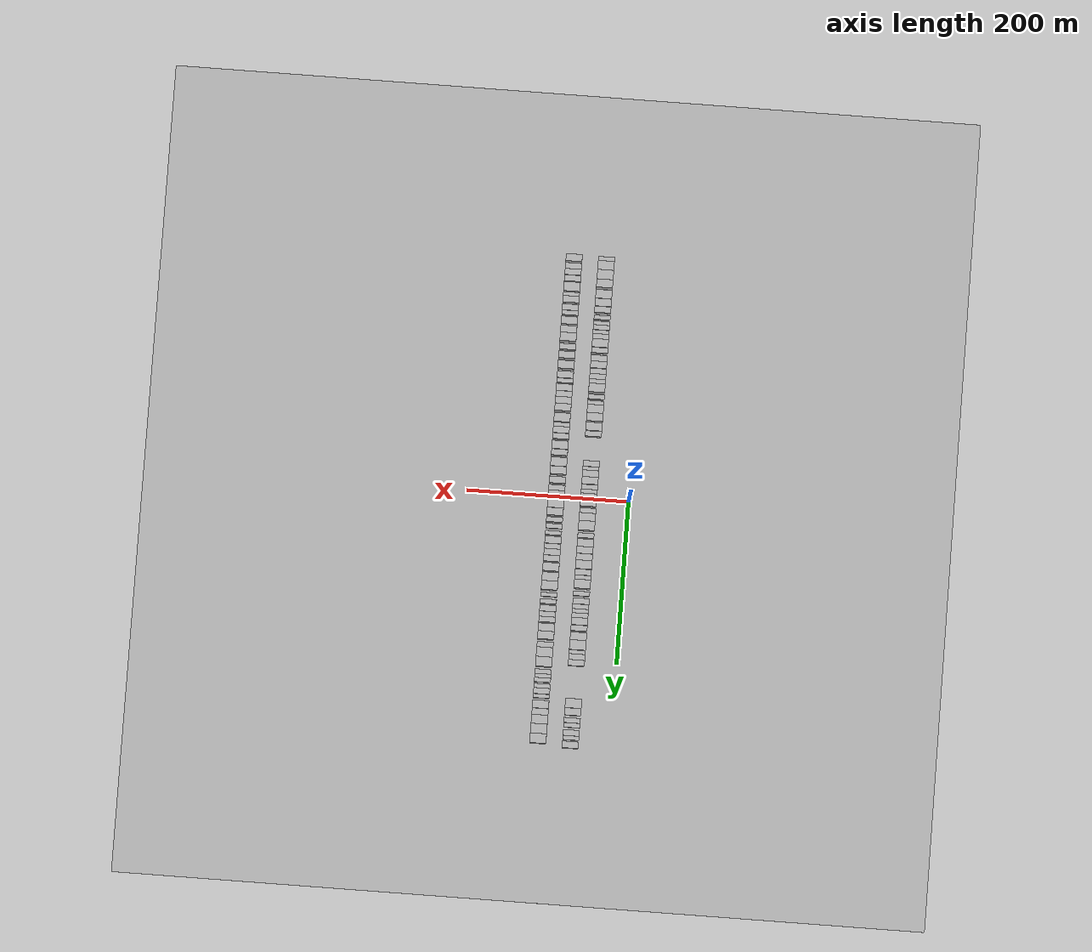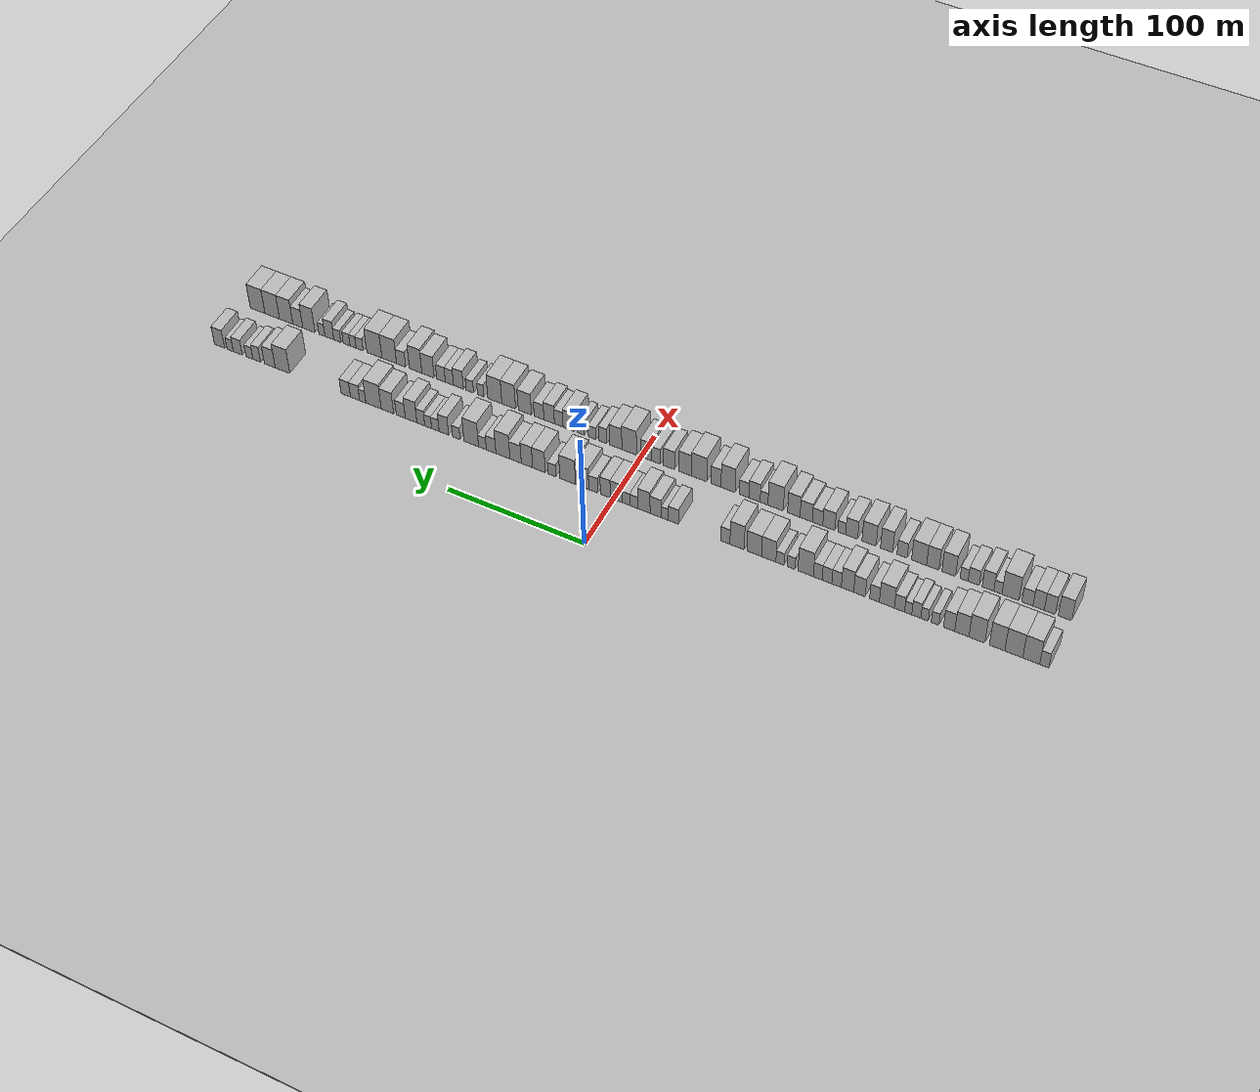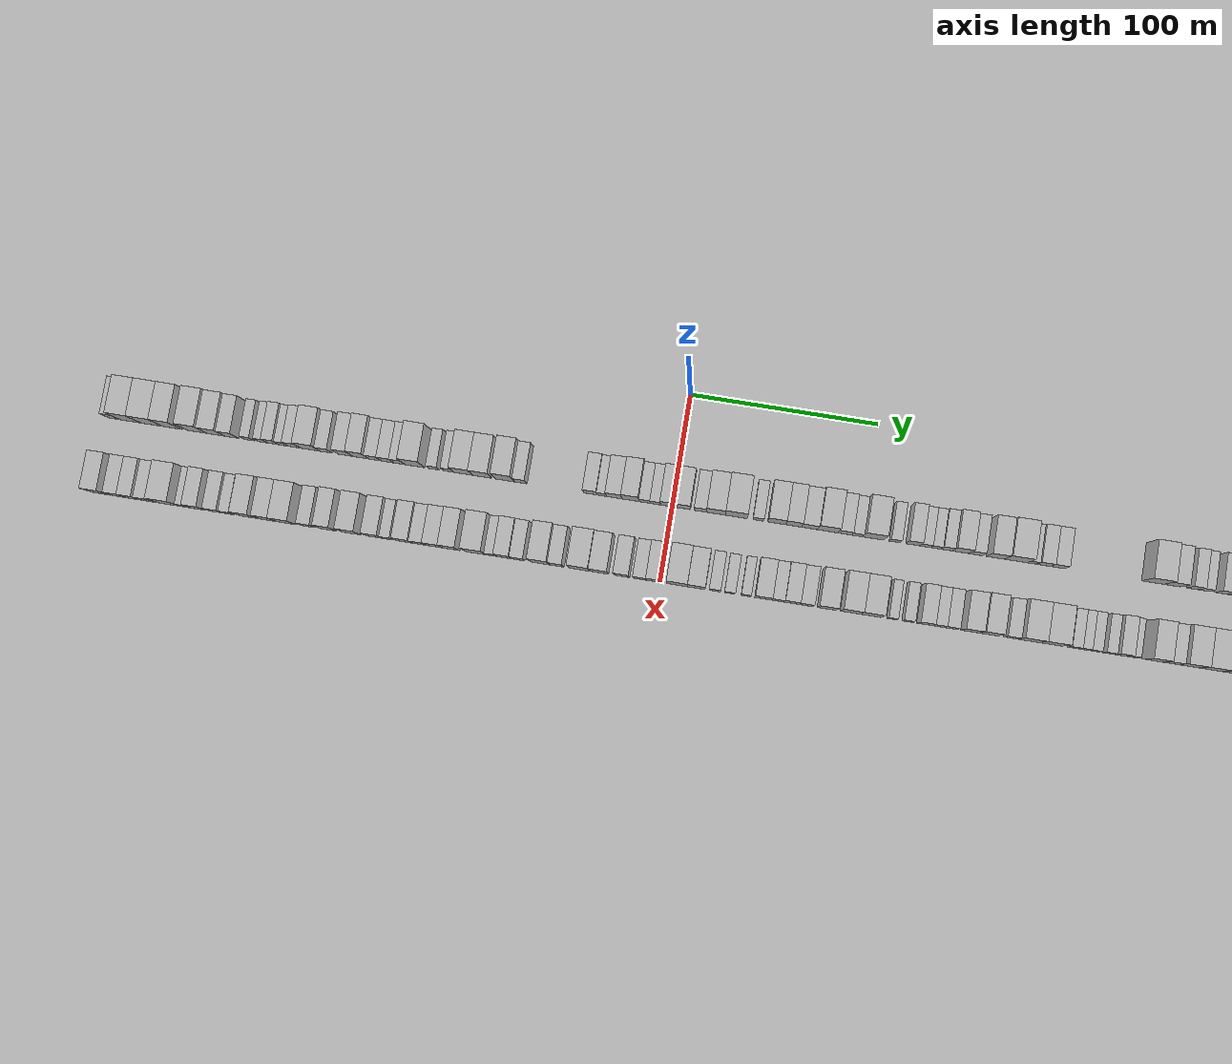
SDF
<?xml version="1.0" encoding="utf-8"?>

<sdf version="1.6">

   <world name="default">

      <gui fullscreen="0">

         <camera name="user_camera">

            <pose>-15 0 4.57585 0 0 0</pose>

            <view_controller>orbit</view_controller>

         </camera>

      </gui>

      <scene>

         <sky>

           <clouds>

             <speed>12</speed>

           </clouds>

         </sky>

         <ambient>0.4 0.4 0.4 1</ambient>

         <background>0.7 0.7 0.7 1</background>

         <shadows>1</shadows>

      </scene>

      <gravity>0 0 -9.8066</gravity>

      <magnetic_field>6e-06 2.3e-05 -4.2e-05</magnetic_field>

      <physics default="0" name="default_physics" type="ode">

         <ode>

            <solver>

               <type>quick</type>

               <iters>10</iters>

               <sor>1.0</sor>

               <use_dynamic_moi_rescaling>0</use_dynamic_moi_rescaling>

            </solver>

            <constraints>

               <cfm>0</cfm>

               <erp>0.2</erp>

               <contact_max_correcting_vel>100</contact_max_correcting_vel>

               <contact_surface_layer>0.001</contact_surface_layer>

            </constraints>

         </ode>

         <max_step_size>0.004</max_step_size>

         <real_time_factor>1</real_time_factor>

         <real_time_update_rate>250</real_time_update_rate>

      </physics>

      <light name="sun" type="directional">

         <cast_shadows>1</cast_shadows>

         <pose>0 0 10 0 0 0</pose>

         <diffuse>0.8 0.8 0.8 1</diffuse>

         <specular>0.2 0.2 0.2 1</specular>

         <attenuation>

            <range>1000</range>

            <constant>0.9</constant>

            <linear>0.01</linear>

            <quadratic>0.001</quadratic>

         </attenuation>

         <direction>-0.5 0.1 -0.9</direction>

      </light>

      <include>

         <name>ground_plane_1</name>

         <uri>model://HANNAS_ground_plane</uri>

         <pose>0 0 0  0 0 0</pose>

      </include>

      <include>

         <name>ground_plane_2</name>

         <uri>model://HANNAS_ground_plane</uri>

         <pose>100 0 0  0 0 0</pose>

      </include>

      <model name="building_1">

         <static>1</static>

         <pose frame="">50.0000 -296.9921 0 0.000000 0.000000 0.000000</pose>

         <link name="link">

            <pose frame="">0 0 7.50 0 0 0</pose>

            <collision name="collision">

               <geometry>

                  <box>

                     <size>20.0000 6.0158 15.0000</size>

                  </box>

               </geometry>

               <max_contacts>10</max_contacts>

               <surface>

                  <contact>

                     <ode/>

                  </contact>

                  <bounce/>

                  <friction>

                     <torsional>

                        <ode/>

                     </torsional>

                     <ode/>

                  </friction>

               </surface>

            </collision>

            <visual name="visual">

               <cast_shadows>0</cast_shadows>

               <geometry>

                  <box>

                     <size>20.0000 6.0158 15.0000</size>

                  </box>

               </geometry>

               <material>

                  <script>

                     <uri>model://HANNAS_wall/materials/scripts</uri>

                     <uri>model://HANNAS_wall/materials/textures</uri>

                     <name>vrc/HANNAS_wall</name>

                  </script>

               </material>

            </visual>

            <self_collide>0</self_collide>

            <enable_wind>0</enable_wind>

            <kinematic>0</kinematic>

         </link>

      </model>

      <model name="building_2">

         <static>1</static>

         <pose frame="">50.0000 -288.4658 0 0.000000 0.000000 0.000000</pose>

         <link name="link">

            <pose frame="">0 0 12.00 0 0 0</pose>

            <collision name="collision">

               <geometry>

                  <box>

                     <size>20.0000 11.0369 24.0000</size>

                  </box>

               </geometry>

               <max_contacts>10</max_contacts>

               <surface>

                  <contact>

                     <ode/>

                  </contact>

                  <bounce/>

                  <friction>

                     <torsional>

                        <ode/>

                     </torsional>

                     <ode/>

                  </friction>

               </surface>

            </collision>

            <visual name="visual">

               <cast_shadows>0</cast_shadows>

               <geometry>

                  <box>

                     <size>20.0000 11.0369 24.0000</size>

                  </box>

               </geometry>

               <material>

                  <script>

                     <uri>model://HANNAS_wall/materials/scripts</uri>

                     <uri>model://HANNAS_wall/materials/textures</uri>

                     <name>vrc/HANNAS_wall</name>

                  </script>

               </material>

            </visual>

            <self_collide>0</self_collide>

            <enable_wind>0</enable_wind>

            <kinematic>0</kinematic>

         </link>

      </model>

      <model name="building_3">

         <static>1</static>

         <pose frame="">50.0000 -277.0403 0 0.000000 0.000000 0.000000</pose>

         <link name="link">

            <pose frame="">0 0 12.00 0 0 0</pose>

            <collision name="collision">

               <geometry>

                  <box>

                     <size>20.0000 11.8140 24.0000</size>

                  </box>

               </geometry>

               <max_contacts>10</max_contacts>

               <surface>

                  <contact>

                     <ode/>

                  </contact>

                  <bounce/>

                  <friction>

                     <torsional>

                        <ode/>

                     </torsional>

                     <ode/>

                  </friction>

               </surface>

            </collision>

            <visual name="visual">

               <cast_shadows>0</cast_shadows>

               <geometry>

                  <box>

                     <size>20.0000 11.8140 24.0000</size>

                  </box>

               </geometry>

               <material>

                  <script>

                     <uri>model://HANNAS_wall/materials/scripts</uri>

                     <uri>model://HANNAS_wall/materials/textures</uri>

                     <name>vrc/HANNAS_wall</name>

                  </script>

               </material>

            </visual>

            <self_collide>0</self_collide>

            <enable_wind>0</enable_wind>

            <kinematic>0</kinematic>

         </link>

      </model>

      <model name="building_4">

         <static>1</static>

         <pose frame="">50.0000 -266.0518 0 0.000000 0.000000 0.000000</pose>

         <link name="link">

            <pose frame="">0 0 12.00 0 0 0</pose>

            <collision name="collision">

               <geometry>

                  <box>

                     <size>20.0000 10.1629 24.0000</size>

                  </box>

               </geometry>

               <max_contacts>10</max_contacts>

               <surface>

                  <contact>

                     <ode/>

                  </contact>

                  <bounce/>

                  <friction>

                     <torsional>

                        <ode/>

                     </torsional>

                     <ode/>

                  </friction>

               </surface>

            </collision>

            <visual name="visual">

               <cast_shadows>0</cast_shadows>

               <geometry>

                  <box>

                     <size>20.0000 10.1629 24.0000</size>

                  </box>

               </geometry>

               <material>

                  <script>

                     <uri>model://HANNAS_wall/materials/scripts</uri>

                     <uri>model://HANNAS_wall/materials/textures</uri>

                     <name>vrc/HANNAS_wall</name>

                  </script>

               </material>

            </visual>

            <self_collide>0</self_collide>

            <enable_wind>0</enable_wind>

            <kinematic>0</kinematic>

         </link>

      </model>

      <model name="building_5">

         <static>1</static>

         <pose frame="">50.0000 -252.6751 0 0.000000 0.000000 0.000000</pose>

         <link name="link">

            <pose frame="">0 0 12.00 0 0 0</pose>

            <collision name="collision">

               <geometry>

                  <box>

                     <size>20.0000 10.5906 24.0000</size>

                  </box>

               </geometry>

               <max_contacts>10</max_contacts>

               <surface>

                  <contact>

                     <ode/>

                  </contact>

                  <bounce/>

                  <friction>

                     <torsional>

                        <ode/>

                     </torsional>

                     <ode/>

                  </friction>

               </surface>

            </collision>

            <visual name="visual">

               <cast_shadows>0</cast_shadows>

               <geometry>

                  <box>

                     <size>20.0000 10.5906 24.0000</size>

                  </box>

               </geometry>

               <material>

                  <script>

                     <uri>model://HANNAS_wall/materials/scripts</uri>

                     <uri>model://HANNAS_wall/materials/textures</uri>

                     <name>vrc/HANNAS_wall</name>

                  </script>

               </material>

            </visual>

            <self_collide>0</self_collide>

            <enable_wind>0</enable_wind>

            <kinematic>0</kinematic>

         </link>

      </model>

      <model name="building_6">

         <static>1</static>

         <pose frame="">50.0000 -242.6532 0 0.000000 0.000000 0.000000</pose>

         <link name="link">

            <pose frame="">0 0 10.50 0 0 0</pose>

            <collision name="collision">

               <geometry>

                  <box>

                     <size>20.0000 9.4532 21.0000</size>

                  </box>

               </geometry>

               <max_contacts>10</max_contacts>

               <surface>

                  <contact>

                     <ode/>

                  </contact>

                  <bounce/>

                  <friction>

                     <torsional>

                        <ode/>

                     </torsional>

                     <ode/>

                  </friction>

               </surface>

            </collision>

            <visual name="visual">

               <cast_shadows>0</cast_shadows>

               <geometry>

                  <box>

                     <size>20.0000 9.4532 21.0000</size>

                  </box>

               </geometry>

               <material>

                  <script>

                     <uri>model://HANNAS_wall/materials/scripts</uri>

                     <uri>model://HANNAS_wall/materials/textures</uri>

                     <name>vrc/HANNAS_wall</name>

                  </script>

               </material>

            </visual>

            <self_collide>0</self_collide>

            <enable_wind>0</enable_wind>

            <kinematic>0</kinematic>

         </link>

      </model>

      <model name="building_7">

         <static>1</static>

         <pose frame="">50.0000 -234.1724 0 0.000000 0.000000 0.000000</pose>

         <link name="link">

            <pose frame="">0 0 9.00 0 0 0</pose>

            <collision name="collision">

               <geometry>

                  <box>

                     <size>20.0000 7.5082 18.0000</size>

                  </box>

               </geometry>

               <max_contacts>10</max_contacts>

               <surface>

                  <contact>

                     <ode/>

                  </contact>

                  <bounce/>

                  <friction>

                     <torsional>

                        <ode/>

                     </torsional>

                     <ode/>

                  </friction>

               </surface>

            </collision>

            <visual name="visual">

               <cast_shadows>0</cast_shadows>

               <geometry>

                  <box>

                     <size>20.0000 7.5082 18.0000</size>

                  </box>

               </geometry>

               <material>

                  <script>

                     <uri>model://HANNAS_wall/materials/scripts</uri>

                     <uri>model://HANNAS_wall/materials/textures</uri>

                     <name>vrc/HANNAS_wall</name>

                  </script>

               </material>

            </visual>

            <self_collide>0</self_collide>

            <enable_wind>0</enable_wind>

            <kinematic>0</kinematic>

         </link>

      </model>

      <model name="building_8">

         <static>1</static>

         <pose frame="">50.0000 -224.8168 0 0.000000 0.000000 0.000000</pose>

         <link name="link">

            <pose frame="">0 0 6.00 0 0 0</pose>

            <collision name="collision">

               <geometry>

                  <box>

                     <size>20.0000 5.2030 12.0000</size>

                  </box>

               </geometry>

               <max_contacts>10</max_contacts>

               <surface>

                  <contact>

                     <ode/>

                  </contact>

                  <bounce/>

                  <friction>

                     <torsional>

                        <ode/>

                     </torsional>

                     <ode/>

                  </friction>

               </surface>

            </collision>

            <visual name="visual">

               <cast_shadows>0</cast_shadows>

               <geometry>

                  <box>

                     <size>20.0000 5.2030 12.0000</size>

                  </box>

               </geometry>

               <material>

                  <script>

                     <uri>model://HANNAS_wall/materials/scripts</uri>

                     <uri>model://HANNAS_wall/materials/textures</uri>

                     <name>vrc/HANNAS_wall</name>

                  </script>

               </material>

            </visual>

            <self_collide>0</self_collide>

            <enable_wind>0</enable_wind>

            <kinematic>0</kinematic>

         </link>

      </model>

      <model name="building_9">

         <static>1</static>

         <pose frame="">50.0000 -217.7098 0 0.000000 0.000000 0.000000</pose>

         <link name="link">

            <pose frame="">0 0 6.00 0 0 0</pose>

            <collision name="collision">

               <geometry>

                  <box>

                     <size>20.0000 5.0111 12.0000</size>

                  </box>

               </geometry>

               <max_contacts>10</max_contacts>

               <surface>

                  <contact>

                     <ode/>

                  </contact>

                  <bounce/>

                  <friction>

                     <torsional>

                        <ode/>

                     </torsional>

                     <ode/>

                  </friction>

               </surface>

            </collision>

            <visual name="visual">

               <cast_shadows>0</cast_shadows>

               <geometry>

                  <box>

                     <size>20.0000 5.0111 12.0000</size>

                  </box>

               </geometry>

               <material>

                  <script>

                     <uri>model://HANNAS_wall/materials/scripts</uri>

                     <uri>model://HANNAS_wall/materials/textures</uri>

                     <name>vrc/HANNAS_wall</name>

                  </script>

               </material>

            </visual>

            <self_collide>0</self_collide>

            <enable_wind>0</enable_wind>

            <kinematic>0</kinematic>

         </link>

      </model>

      <model name="building_10">

         <static>1</static>

         <pose frame="">50.0000 -212.1757 0 0.000000 0.000000 0.000000</pose>

         <link name="link">

            <pose frame="">0 0 7.50 0 0 0</pose>

            <collision name="collision">

               <geometry>

                  <box>

                     <size>20.0000 6.0572 15.0000</size>

                  </box>

               </geometry>

               <max_contacts>10</max_contacts>

               <surface>

                  <contact>

                     <ode/>

                  </contact>

                  <bounce/>

                  <friction>

                     <torsional>

                        <ode/>

                     </torsional>

                     <ode/>

                  </friction>

               </surface>

            </collision>

            <visual name="visual">

               <cast_shadows>0</cast_shadows>

               <geometry>

                  <box>

                     <size>20.0000 6.0572 15.0000</size>

                  </box>

               </geometry>

               <material>

                  <script>

                     <uri>model://HANNAS_wall/materials/scripts</uri>

                     <uri>model://HANNAS_wall/materials/textures</uri>

                     <name>vrc/HANNAS_wall</name>

                  </script>

               </material>

            </visual>

            <self_collide>0</self_collide>

            <enable_wind>0</enable_wind>

            <kinematic>0</kinematic>

         </link>

      </model>

      <model name="building_11">

         <static>1</static>

         <pose frame="">50.0000 -206.6927 0 0.000000 0.000000 0.000000</pose>

         <link name="link">

            <pose frame="">0 0 6.00 0 0 0</pose>

            <collision name="collision">

               <geometry>

                  <box>

                     <size>20.0000 4.9087 12.0000</size>

                  </box>

               </geometry>

               <max_contacts>10</max_contacts>

               <surface>

                  <contact>

                     <ode/>

                  </contact>

                  <bounce/>

                  <friction>

                     <torsional>

                        <ode/>

                     </torsional>

                     <ode/>

                  </friction>

               </surface>

            </collision>

            <visual name="visual">

               <cast_shadows>0</cast_shadows>

               <geometry>

                  <box>

                     <size>20.0000 4.9087 12.0000</size>

                  </box>

               </geometry>

               <material>

                  <script>

                     <uri>model://HANNAS_wall/materials/scripts</uri>

                     <uri>model://HANNAS_wall/materials/textures</uri>

                     <name>vrc/HANNAS_wall</name>

                  </script>

               </material>

            </visual>

            <self_collide>0</self_collide>

            <enable_wind>0</enable_wind>

            <kinematic>0</kinematic>

         </link>

      </model>

      <model name="building_12">

         <static>1</static>

         <pose frame="">50.0000 -200.7944 0 0.000000 0.000000 0.000000</pose>

         <link name="link">

            <pose frame="">0 0 7.50 0 0 0</pose>

            <collision name="collision">

               <geometry>

                  <box>

                     <size>20.0000 6.8878 15.0000</size>

                  </box>

               </geometry>

               <max_contacts>10</max_contacts>

               <surface>

                  <contact>

                     <ode/>

                  </contact>

                  <bounce/>

                  <friction>

                     <torsional>

                        <ode/>

                     </torsional>

                     <ode/>

                  </friction>

               </surface>

            </collision>

            <visual name="visual">

               <cast_shadows>0</cast_shadows>

               <geometry>

                  <box>

                     <size>20.0000 6.8878 15.0000</size>

                  </box>

               </geometry>

               <material>

                  <script>

                     <uri>model://HANNAS_wall/materials/scripts</uri>

                     <uri>model://HANNAS_wall/materials/textures</uri>

                     <name>vrc/HANNAS_wall</name>

                  </script>

               </material>

            </visual>

            <self_collide>0</self_collide>

            <enable_wind>0</enable_wind>

            <kinematic>0</kinematic>

         </link>

      </model>

      <model name="building_13">

         <static>1</static>

         <pose frame="">50.0000 -192.2591 0 0.000000 0.000000 0.000000</pose>

         <link name="link">

            <pose frame="">0 0 10.50 0 0 0</pose>

            <collision name="collision">

               <geometry>

                  <box>

                     <size>20.0000 10.1827 21.0000</size>

                  </box>

               </geometry>

               <max_contacts>10</max_contacts>

               <surface>

                  <contact>

                     <ode/>

                  </contact>

                  <bounce/>

                  <friction>

                     <torsional>

                        <ode/>

                     </torsional>

                     <ode/>

                  </friction>

               </surface>

            </collision>

            <visual name="visual">

               <cast_shadows>0</cast_shadows>

               <geometry>

                  <box>

                     <size>20.0000 10.1827 21.0000</size>

                  </box>

               </geometry>

               <material>

                  <script>

                     <uri>model://HANNAS_wall/materials/scripts</uri>

                     <uri>model://HANNAS_wall/materials/textures</uri>

                     <name>vrc/HANNAS_wall</name>

                  </script>

               </material>

            </visual>

            <self_collide>0</self_collide>

            <enable_wind>0</enable_wind>

            <kinematic>0</kinematic>

         </link>

      </model>

      <model name="building_14">

         <static>1</static>

         <pose frame="">50.0000 -183.8532 0 0.000000 0.000000 0.000000</pose>

         <link name="link">

            <pose frame="">0 0 7.50 0 0 0</pose>

            <collision name="collision">

               <geometry>

                  <box>

                     <size>20.0000 6.6292 15.0000</size>

                  </box>

               </geometry>

               <max_contacts>10</max_contacts>

               <surface>

                  <contact>

                     <ode/>

                  </contact>

                  <bounce/>

                  <friction>

                     <torsional>

                        <ode/>

                     </torsional>

                     <ode/>

                  </friction>

               </surface>

            </collision>

            <visual name="visual">

               <cast_shadows>0</cast_shadows>

               <geometry>

                  <box>

                     <size>20.0000 6.6292 15.0000</size>

                  </box>

               </geometry>

               <material>

                  <script>

                     <uri>model://HANNAS_wall/materials/scripts</uri>

                     <uri>model://HANNAS_wall/materials/textures</uri>

                     <name>vrc/HANNAS_wall</name>

                  </script>

               </material>

            </visual>

            <self_collide>0</self_collide>

            <enable_wind>0</enable_wind>

            <kinematic>0</kinematic>

         </link>

      </model>

      <model name="building_15">

         <static>1</static>

         <pose frame="">50.0000 -173.6080 0 0.000000 0.000000 0.000000</pose>

         <link name="link">

            <pose frame="">0 0 9.00 0 0 0</pose>

            <collision name="collision">

               <geometry>

                  <box>

                     <size>20.0000 7.8611 18.0000</size>

                  </box>

               </geometry>

               <max_contacts>10</max_contacts>

               <surface>

                  <contact>

                     <ode/>

                  </contact>

                  <bounce/>

                  <friction>

                     <torsional>

                        <ode/>

                     </torsional>

                     <ode/>

                  </friction>

               </surface>

            </collision>

            <visual name="visual">

               <cast_shadows>0</cast_shadows>

               <geometry>

                  <box>

                     <size>20.0000 7.8611 18.0000</size>

                  </box>

               </geometry>

               <material>

                  <script>

                     <uri>model://HANNAS_wall/materials/scripts</uri>

                     <uri>model://HANNAS_wall/materials/textures</uri>

                     <name>vrc/HANNAS_wall</name>

                  </script>

               </material>

            </visual>

            <self_collide>0</self_collide>

            <enable_wind>0</enable_wind>

            <kinematic>0</kinematic>

         </link>

      </model>

      <model name="building_16">

         <static>1</static>

         <pose frame="">50.0000 -165.4224 0 0.000000 0.000000 0.000000</pose>

         <link name="link">

            <pose frame="">0 0 10.50 0 0 0</pose>

            <collision name="collision">

               <geometry>

                  <box>

                     <size>20.0000 8.5100 21.0000</size>

                  </box>

               </geometry>

               <max_contacts>10</max_contacts>

               <surface>

                  <contact>

                     <ode/>

                  </contact>

                  <bounce/>

                  <friction>

                     <torsional>

                        <ode/>

                     </torsional>

                     <ode/>

                  </friction>

               </surface>

            </collision>

            <visual name="visual">

               <cast_shadows>0</cast_shadows>

               <geometry>

                  <box>

                     <size>20.0000 8.5100 21.0000</size>

                  </box>

               </geometry>

               <material>

                  <script>

                     <uri>model://HANNAS_wall/materials/scripts</uri>

                     <uri>model://HANNAS_wall/materials/textures</uri>

                     <name>vrc/HANNAS_wall</name>

                  </script>

               </material>

            </visual>

            <self_collide>0</self_collide>

            <enable_wind>0</enable_wind>

            <kinematic>0</kinematic>

         </link>

      </model>

      <model name="building_17">

         <static>1</static>

         <pose frame="">50.0000 -157.9158 0 0.000000 0.000000 0.000000</pose>

         <link name="link">

            <pose frame="">0 0 7.50 0 0 0</pose>

            <collision name="collision">

               <geometry>

                  <box>

                     <size>20.0000 6.5033 15.0000</size>

                  </box>

               </geometry>

               <max_contacts>10</max_contacts>

               <surface>

                  <contact>

                     <ode/>

                  </contact>

                  <bounce/>

                  <friction>

                     <torsional>

                        <ode/>

                     </torsional>

                     <ode/>

                  </friction>

               </surface>

            </collision>

            <visual name="visual">

               <cast_shadows>0</cast_shadows>

               <geometry>

                  <box>

                     <size>20.0000 6.5033 15.0000</size>

                  </box>

               </geometry>

               <material>

                  <script>

                     <uri>model://HANNAS_wall/materials/scripts</uri>

                     <uri>model://HANNAS_wall/materials/textures</uri>

                     <name>vrc/HANNAS_wall</name>

                  </script>

               </material>

            </visual>

            <self_collide>0</self_collide>

            <enable_wind>0</enable_wind>

            <kinematic>0</kinematic>

         </link>

      </model>

      <model name="building_18">

         <static>1</static>

         <pose frame="">50.0000 -151.3319 0 0.000000 0.000000 0.000000</pose>

         <link name="link">

            <pose frame="">0 0 7.50 0 0 0</pose>

            <collision name="collision">

               <geometry>

                  <box>

                     <size>20.0000 6.6644 15.0000</size>

                  </box>

               </geometry>

               <max_contacts>10</max_contacts>

               <surface>

                  <contact>

                     <ode/>

                  </contact>

                  <bounce/>

                  <friction>

                     <torsional>

                        <ode/>

                     </torsional>

                     <ode/>

                  </friction>

               </surface>

            </collision>

            <visual name="visual">

               <cast_shadows>0</cast_shadows>

               <geometry>

                  <box>

                     <size>20.0000 6.6644 15.0000</size>

                  </box>

               </geometry>

               <material>

                  <script>

                     <uri>model://HANNAS_wall/materials/scripts</uri>

                     <uri>model://HANNAS_wall/materials/textures</uri>

                     <name>vrc/HANNAS_wall</name>

                  </script>

               </material>

            </visual>

            <self_collide>0</self_collide>

            <enable_wind>0</enable_wind>

            <kinematic>0</kinematic>

         </link>

      </model>

      <model name="building_19">

         <static>1</static>

         <pose frame="">50.0000 -144.9612 0 0.000000 0.000000 0.000000</pose>

         <link name="link">

            <pose frame="">0 0 7.50 0 0 0</pose>

            <collision name="collision">

               <geometry>

                  <box>

                     <size>20.0000 6.0769 15.0000</size>

                  </box>

               </geometry>

               <max_contacts>10</max_contacts>

               <surface>

                  <contact>

                     <ode/>

                  </contact>

                  <bounce/>

                  <friction>

                     <torsional>

                        <ode/>

                     </torsional>

                     <ode/>

                  </friction>

               </surface>

            </collision>

            <visual name="visual">

               <cast_shadows>0</cast_shadows>

               <geometry>

                  <box>

                     <size>20.0000 6.0769 15.0000</size>

                  </box>

               </geometry>

               <material>

                  <script>

                     <uri>model://HANNAS_wall/materials/scripts</uri>

                     <uri>model://HANNAS_wall/materials/textures</uri>

                     <name>vrc/HANNAS_wall</name>

                  </script>

               </material>

            </visual>

            <self_collide>0</self_collide>

            <enable_wind>0</enable_wind>

            <kinematic>0</kinematic>

         </link>

      </model>

      <model name="building_20">

         <static>1</static>

         <pose frame="">50.0000 -136.5913 0 0.000000 0.000000 0.000000</pose>

         <link name="link">

            <pose frame="">0 0 12.00 0 0 0</pose>

            <collision name="collision">

               <geometry>

                  <box>

                     <size>20.0000 10.6628 24.0000</size>

                  </box>

               </geometry>

               <max_contacts>10</max_contacts>

               <surface>

                  <contact>

                     <ode/>

                  </contact>

                  <bounce/>

                  <friction>

                     <torsional>

                        <ode/>

                     </torsional>

                     <ode/>

                  </friction>

               </surface>

            </collision>

            <visual name="visual">

               <cast_shadows>0</cast_shadows>

               <geometry>

                  <box>

                     <size>20.0000 10.6628 24.0000</size>

                  </box>

               </geometry>

               <material>

                  <script>

                     <uri>model://HANNAS_wall/materials/scripts</uri>

                     <uri>model://HANNAS_wall/materials/textures</uri>

                     <name>vrc/HANNAS_wall</name>

                  </script>

               </material>

            </visual>

            <self_collide>0</self_collide>

            <enable_wind>0</enable_wind>

            <kinematic>0</kinematic>

         </link>

      </model>

      <model name="building_21">

         <static>1</static>

         <pose frame="">50.0000 -126.3974 0 0.000000 0.000000 0.000000</pose>

         <link name="link">

            <pose frame="">0 0 6.00 0 0 0</pose>

            <collision name="collision">

               <geometry>

                  <box>

                     <size>20.0000 5.7250 12.0000</size>

                  </box>

               </geometry>

               <max_contacts>10</max_contacts>

               <surface>

                  <contact>

                     <ode/>

                  </contact>

                  <bounce/>

                  <friction>

                     <torsional>

                        <ode/>

                     </torsional>

                     <ode/>

                  </friction>

               </surface>

            </collision>

            <visual name="visual">

               <cast_shadows>0</cast_shadows>

               <geometry>

                  <box>

                     <size>20.0000 5.7250 12.0000</size>

                  </box>

               </geometry>

               <material>

                  <script>

                     <uri>model://HANNAS_wall/materials/scripts</uri>

                     <uri>model://HANNAS_wall/materials/textures</uri>

                     <name>vrc/HANNAS_wall</name>

                  </script>

               </material>

            </visual>

            <self_collide>0</self_collide>

            <enable_wind>0</enable_wind>

            <kinematic>0</kinematic>

         </link>

      </model>

      <model name="building_22">

         <static>1</static>

         <pose frame="">50.0000 -118.7112 0 0.000000 0.000000 0.000000</pose>

         <link name="link">

            <pose frame="">0 0 6.00 0 0 0</pose>

            <collision name="collision">

               <geometry>

                  <box>

                     <size>20.0000 5.6475 12.0000</size>

                  </box>

               </geometry>

               <max_contacts>10</max_contacts>

               <surface>

                  <contact>

                     <ode/>

                  </contact>

                  <bounce/>

                  <friction>

                     <torsional>

                        <ode/>

                     </torsional>

                     <ode/>

                  </friction>

               </surface>

            </collision>

            <visual name="visual">

               <cast_shadows>0</cast_shadows>

               <geometry>

                  <box>

                     <size>20.0000 5.6475 12.0000</size>

                  </box>

               </geometry>

               <material>

                  <script>

                     <uri>model://HANNAS_wall/materials/scripts</uri>

                     <uri>model://HANNAS_wall/materials/textures</uri>

                     <name>vrc/HANNAS_wall</name>

                  </script>

               </material>

            </visual>

            <self_collide>0</self_collide>

            <enable_wind>0</enable_wind>

            <kinematic>0</kinematic>

         </link>

      </model>

      <model name="building_23">

         <static>1</static>

         <pose frame="">50.0000 -110.8488 0 0.000000 0.000000 0.000000</pose>

         <link name="link">

            <pose frame="">0 0 10.50 0 0 0</pose>

            <collision name="collision">

               <geometry>

                  <box>

                     <size>20.0000 10.0774 21.0000</size>

                  </box>

               </geometry>

               <max_contacts>10</max_contacts>

               <surface>

                  <contact>

                     <ode/>

                  </contact>

                  <bounce/>

                  <friction>

                     <torsional>

                        <ode/>

                     </torsional>

                     <ode/>

                  </friction>

               </surface>

            </collision>

            <visual name="visual">

               <cast_shadows>0</cast_shadows>

               <geometry>

                  <box>

                     <size>20.0000 10.0774 21.0000</size>

                  </box>

               </geometry>

               <material>

                  <script>

                     <uri>model://HANNAS_wall/materials/scripts</uri>

                     <uri>model://HANNAS_wall/materials/textures</uri>

                     <name>vrc/HANNAS_wall</name>

                  </script>

               </material>

            </visual>

            <self_collide>0</self_collide>

            <enable_wind>0</enable_wind>

            <kinematic>0</kinematic>

         </link>

      </model>

      <model name="building_24">

         <static>1</static>

         <pose frame="">50.0000 -100.7308 0 0.000000 0.000000 0.000000</pose>

         <link name="link">

            <pose frame="">0 0 10.50 0 0 0</pose>

            <collision name="collision">

               <geometry>

                  <box>

                     <size>20.0000 10.1586 21.0000</size>

                  </box>

               </geometry>

               <max_contacts>10</max_contacts>

               <surface>

                  <contact>

                     <ode/>

                  </contact>

                  <bounce/>

                  <friction>

                     <torsional>

                        <ode/>

                     </torsional>

                     <ode/>

                  </friction>

               </surface>

            </collision>

            <visual name="visual">

               <cast_shadows>0</cast_shadows>

               <geometry>

                  <box>

                     <size>20.0000 10.1586 21.0000</size>

                  </box>

               </geometry>

               <material>

                  <script>

                     <uri>model://HANNAS_wall/materials/scripts</uri>

                     <uri>model://HANNAS_wall/materials/textures</uri>

                     <name>vrc/HANNAS_wall</name>

                  </script>

               </material>

            </visual>

            <self_collide>0</self_collide>

            <enable_wind>0</enable_wind>

            <kinematic>0</kinematic>

         </link>

      </model>

      <model name="building_25">

         <static>1</static>

         <pose frame="">50.0000 -88.6149 0 0.000000 0.000000 0.000000</pose>

         <link name="link">

            <pose frame="">0 0 12.00 0 0 0</pose>

            <collision name="collision">

               <geometry>

                  <box>

                     <size>20.0000 10.0731 24.0000</size>

                  </box>

               </geometry>

               <max_contacts>10</max_contacts>

               <surface>

                  <contact>

                     <ode/>

                  </contact>

                  <bounce/>

                  <friction>

                     <torsional>

                        <ode/>

                     </torsional>

                     <ode/>

                  </friction>

               </surface>

            </collision>

            <visual name="visual">

               <cast_shadows>0</cast_shadows>

               <geometry>

                  <box>

                     <size>20.0000 10.0731 24.0000</size>

                  </box>

               </geometry>

               <material>

                  <script>

                     <uri>model://HANNAS_wall/materials/scripts</uri>

                     <uri>model://HANNAS_wall/materials/textures</uri>

                     <name>vrc/HANNAS_wall</name>

                  </script>

               </material>

            </visual>

            <self_collide>0</self_collide>

            <enable_wind>0</enable_wind>

            <kinematic>0</kinematic>

         </link>

      </model>

      <model name="building_26">

         <static>1</static>

         <pose frame="">50.0000 -80.3143 0 0.000000 0.000000 0.000000</pose>

         <link name="link">

            <pose frame="">0 0 7.50 0 0 0</pose>

            <collision name="collision">

               <geometry>

                  <box>

                     <size>20.0000 6.5280 15.0000</size>

                  </box>

               </geometry>

               <max_contacts>10</max_contacts>

               <surface>

                  <contact>

                     <ode/>

                  </contact>

                  <bounce/>

                  <friction>

                     <torsional>

                        <ode/>

                     </torsional>

                     <ode/>

                  </friction>

               </surface>

            </collision>

            <visual name="visual">

               <cast_shadows>0</cast_shadows>

               <geometry>

                  <box>

                     <size>20.0000 6.5280 15.0000</size>

                  </box>

               </geometry>

               <material>

                  <script>

                     <uri>model://HANNAS_wall/materials/scripts</uri>

                     <uri>model://HANNAS_wall/materials/textures</uri>

                     <name>vrc/HANNAS_wall</name>

                  </script>

               </material>

            </visual>

            <self_collide>0</self_collide>

            <enable_wind>0</enable_wind>

            <kinematic>0</kinematic>

         </link>

      </model>

      <model name="building_27">

         <static>1</static>

         <pose frame="">50.0000 -43.2637 0 0.000000 0.000000 0.000000</pose>

         <link name="link">

            <pose frame="">0 0 7.50 0 0 0</pose>

            <collision name="collision">

               <geometry>

                  <box>

                     <size>20.0000 7.1911 15.0000</size>

                  </box>

               </geometry>

               <max_contacts>10</max_contacts>

               <surface>

                  <contact>

                     <ode/>

                  </contact>

                  <bounce/>

                  <friction>

                     <torsional>

                        <ode/>

                     </torsional>

                     <ode/>

                  </friction>

               </surface>

            </collision>

            <visual name="visual">

               <cast_shadows>0</cast_shadows>

               <geometry>

                  <box>

                     <size>20.0000 7.1911 15.0000</size>

                  </box>

               </geometry>

               <material>

                  <script>

                     <uri>model://HANNAS_wall/materials/scripts</uri>

                     <uri>model://HANNAS_wall/materials/textures</uri>

                     <name>vrc/HANNAS_wall</name>

                  </script>

               </material>

            </visual>

            <self_collide>0</self_collide>

            <enable_wind>0</enable_wind>

            <kinematic>0</kinematic>

         </link>

      </model>

      <model name="building_28">

         <static>1</static>

         <pose frame="">50.0000 -37.2475 0 0.000000 0.000000 0.000000</pose>

         <link name="link">

            <pose frame="">0 0 6.00 0 0 0</pose>

            <collision name="collision">

               <geometry>

                  <box>

                     <size>20.0000 4.8413 12.0000</size>

                  </box>

               </geometry>

               <max_contacts>10</max_contacts>

               <surface>

                  <contact>

                     <ode/>

                  </contact>

                  <bounce/>

                  <friction>

                     <torsional>

                        <ode/>

                     </torsional>

                     <ode/>

                  </friction>

               </surface>

            </collision>

            <visual name="visual">

               <cast_shadows>0</cast_shadows>

               <geometry>

                  <box>

                     <size>20.0000 4.8413 12.0000</size>

                  </box>

               </geometry>

               <material>

                  <script>

                     <uri>model://HANNAS_wall/materials/scripts</uri>

                     <uri>model://HANNAS_wall/materials/textures</uri>

                     <name>vrc/HANNAS_wall</name>

                  </script>

               </material>

            </visual>

            <self_collide>0</self_collide>

            <enable_wind>0</enable_wind>

            <kinematic>0</kinematic>

         </link>

      </model>

      <model name="building_29">

         <static>1</static>

         <pose frame="">50.0000 -30.6591 0 0.000000 0.000000 0.000000</pose>

         <link name="link">

            <pose frame="">0 0 9.00 0 0 0</pose>

            <collision name="collision">

               <geometry>

                  <box>

                     <size>20.0000 8.3355 18.0000</size>

                  </box>

               </geometry>

               <max_contacts>10</max_contacts>

               <surface>

                  <contact>

                     <ode/>

                  </contact>

                  <bounce/>

                  <friction>

                     <torsional>

                        <ode/>

                     </torsional>

                     <ode/>

                  </friction>

               </surface>

            </collision>

            <visual name="visual">

               <cast_shadows>0</cast_shadows>

               <geometry>

                  <box>

                     <size>20.0000 8.3355 18.0000</size>

                  </box>

               </geometry>

               <material>

                  <script>

                     <uri>model://HANNAS_wall/materials/scripts</uri>

                     <uri>model://HANNAS_wall/materials/textures</uri>

                     <name>vrc/HANNAS_wall</name>

                  </script>

               </material>

            </visual>

            <self_collide>0</self_collide>

            <enable_wind>0</enable_wind>

            <kinematic>0</kinematic>

         </link>

      </model>

      <model name="building_30">

         <static>1</static>

         <pose frame="">50.0000 -22.0079 0 0.000000 0.000000 0.000000</pose>

         <link name="link">

            <pose frame="">0 0 10.50 0 0 0</pose>

            <collision name="collision">

               <geometry>

                  <box>

                     <size>20.0000 8.9668 21.0000</size>

                  </box>

               </geometry>

               <max_contacts>10</max_contacts>

               <surface>

                  <contact>

                     <ode/>

                  </contact>

                  <bounce/>

                  <friction>

                     <torsional>

                        <ode/>

                     </torsional>

                     <ode/>

                  </friction>

               </surface>

            </collision>

            <visual name="visual">

               <cast_shadows>0</cast_shadows>

               <geometry>

                  <box>

                     <size>20.0000 8.9668 21.0000</size>

                  </box>

               </geometry>

               <material>

                  <script>

                     <uri>model://HANNAS_wall/materials/scripts</uri>

                     <uri>model://HANNAS_wall/materials/textures</uri>

                     <name>vrc/HANNAS_wall</name>

                  </script>

               </material>

            </visual>

            <self_collide>0</self_collide>

            <enable_wind>0</enable_wind>

            <kinematic>0</kinematic>

         </link>

      </model>

      <model name="building_31">

         <static>1</static>

         <pose frame="">50.0000 -14.6391 0 0.000000 0.000000 0.000000</pose>

         <link name="link">

            <pose frame="">0 0 6.00 0 0 0</pose>

            <collision name="collision">

               <geometry>

                  <box>

                     <size>20.0000 5.7708 12.0000</size>

                  </box>

               </geometry>

               <max_contacts>10</max_contacts>

               <surface>

                  <contact>

                     <ode/>

                  </contact>

                  <bounce/>

                  <friction>

                     <torsional>

                        <ode/>

                     </torsional>

                     <ode/>

                  </friction>

               </surface>

            </collision>

            <visual name="visual">

               <cast_shadows>0</cast_shadows>

               <geometry>

                  <box>

                     <size>20.0000 5.7708 12.0000</size>

                  </box>

               </geometry>

               <material>

                  <script>

                     <uri>model://HANNAS_wall/materials/scripts</uri>

                     <uri>model://HANNAS_wall/materials/textures</uri>

                     <name>vrc/HANNAS_wall</name>

                  </script>

               </material>

            </visual>

            <self_collide>0</self_collide>

            <enable_wind>0</enable_wind>

            <kinematic>0</kinematic>

         </link>

      </model>

      <model name="building_32">

         <static>1</static>

         <pose frame="">50.0000 -9.0255 0 0.000000 0.000000 0.000000</pose>

         <link name="link">

            <pose frame="">0 0 6.00 0 0 0</pose>

            <collision name="collision">

               <geometry>

                  <box>

                     <size>20.0000 5.4564 12.0000</size>

                  </box>

               </geometry>

               <max_contacts>10</max_contacts>

               <surface>

                  <contact>

                     <ode/>

                  </contact>

                  <bounce/>

                  <friction>

                     <torsional>

                        <ode/>

                     </torsional>

                     <ode/>

                  </friction>

               </surface>

            </collision>

            <visual name="visual">

               <cast_shadows>0</cast_shadows>

               <geometry>

                  <box>

                     <size>20.0000 5.4564 12.0000</size>

                  </box>

               </geometry>

               <material>

                  <script>

                     <uri>model://HANNAS_wall/materials/scripts</uri>

                     <uri>model://HANNAS_wall/materials/textures</uri>

                     <name>vrc/HANNAS_wall</name>

                  </script>

               </material>

            </visual>

            <self_collide>0</self_collide>

            <enable_wind>0</enable_wind>

            <kinematic>0</kinematic>

         </link>

      </model>

      <model name="building_33">

         <static>1</static>

         <pose frame="">50.0000 -1.9753 0 0.000000 0.000000 0.000000</pose>

         <link name="link">

            <pose frame="">0 0 9.00 0 0 0</pose>

            <collision name="collision">

               <geometry>

                  <box>

                     <size>20.0000 8.6439 18.0000</size>

                  </box>

               </geometry>

               <max_contacts>10</max_contacts>

               <surface>

                  <contact>

                     <ode/>

                  </contact>

                  <bounce/>

                  <friction>

                     <torsional>

                        <ode/>

                     </torsional>

                     <ode/>

                  </friction>

               </surface>

            </collision>

            <visual name="visual">

               <cast_shadows>0</cast_shadows>

               <geometry>

                  <box>

                     <size>20.0000 8.6439 18.0000</size>

                  </box>

               </geometry>

               <material>

                  <script>

                     <uri>model://HANNAS_wall/materials/scripts</uri>

                     <uri>model://HANNAS_wall/materials/textures</uri>

                     <name>vrc/HANNAS_wall</name>

                  </script>

               </material>

            </visual>

            <self_collide>0</self_collide>

            <enable_wind>0</enable_wind>

            <kinematic>0</kinematic>

         </link>

      </model>

      <model name="building_34">

         <static>1</static>

         <pose frame="">50.0000 5.9675 0 0.000000 0.000000 0.000000</pose>

         <link name="link">

            <pose frame="">0 0 9.00 0 0 0</pose>

            <collision name="collision">

               <geometry>

                  <box>

                     <size>20.0000 7.2417 18.0000</size>

                  </box>

               </geometry>

               <max_contacts>10</max_contacts>

               <surface>

                  <contact>

                     <ode/>

                  </contact>

                  <bounce/>

                  <friction>

                     <torsional>

                        <ode/>

                     </torsional>

                     <ode/>

                  </friction>

               </surface>

            </collision>

            <visual name="visual">

               <cast_shadows>0</cast_shadows>

               <geometry>

                  <box>

                     <size>20.0000 7.2417 18.0000</size>

                  </box>

               </geometry>

               <material>

                  <script>

                     <uri>model://HANNAS_wall/materials/scripts</uri>

                     <uri>model://HANNAS_wall/materials/textures</uri>

                     <name>vrc/HANNAS_wall</name>

                  </script>

               </material>

            </visual>

            <self_collide>0</self_collide>

            <enable_wind>0</enable_wind>

            <kinematic>0</kinematic>

         </link>

      </model>

      <model name="building_35">

         <static>1</static>

         <pose frame="">50.0000 14.8578 0 0.000000 0.000000 0.000000</pose>

         <link name="link">

            <pose frame="">0 0 7.50 0 0 0</pose>

            <collision name="collision">

               <geometry>

                  <box>

                     <size>20.0000 6.5390 15.0000</size>

                  </box>

               </geometry>

               <max_contacts>10</max_contacts>

               <surface>

                  <contact>

                     <ode/>

                  </contact>

                  <bounce/>

                  <friction>

                     <torsional>

                        <ode/>

                     </torsional>

                     <ode/>

                  </friction>

               </surface>

            </collision>

            <visual name="visual">

               <cast_shadows>0</cast_shadows>

               <geometry>

                  <box>

                     <size>20.0000 6.5390 15.0000</size>

                  </box>

               </geometry>

               <material>

                  <script>

                     <uri>model://HANNAS_wall/materials/scripts</uri>

                     <uri>model://HANNAS_wall/materials/textures</uri>

                     <name>vrc/HANNAS_wall</name>

                  </script>

               </material>

            </visual>

            <self_collide>0</self_collide>

            <enable_wind>0</enable_wind>

            <kinematic>0</kinematic>

         </link>

      </model>

      <model name="building_36">

         <static>1</static>

         <pose frame="">50.0000 23.0570 0 0.000000 0.000000 0.000000</pose>

         <link name="link">

            <pose frame="">0 0 10.50 0 0 0</pose>

            <collision name="collision">

               <geometry>

                  <box>

                     <size>20.0000 9.8593 21.0000</size>

                  </box>

               </geometry>

               <max_contacts>10</max_contacts>

               <surface>

                  <contact>

                     <ode/>

                  </contact>

                  <bounce/>

                  <friction>

                     <torsional>

                        <ode/>

                     </torsional>

                     <ode/>

                  </friction>

               </surface>

            </collision>

            <visual name="visual">

               <cast_shadows>0</cast_shadows>

               <geometry>

                  <box>

                     <size>20.0000 9.8593 21.0000</size>

                  </box>

               </geometry>

               <material>

                  <script>

                     <uri>model://HANNAS_wall/materials/scripts</uri>

                     <uri>model://HANNAS_wall/materials/textures</uri>

                     <name>vrc/HANNAS_wall</name>

                  </script>

               </material>

            </visual>

            <self_collide>0</self_collide>

            <enable_wind>0</enable_wind>

            <kinematic>0</kinematic>

         </link>

      </model>

      <model name="building_37">

         <static>1</static>

         <pose frame="">50.0000 33.7391 0 0.000000 0.000000 0.000000</pose>

         <link name="link">

            <pose frame="">0 0 12.00 0 0 0</pose>

            <collision name="collision">

               <geometry>

                  <box>

                     <size>20.0000 11.5049 24.0000</size>

                  </box>

               </geometry>

               <max_contacts>10</max_contacts>

               <surface>

                  <contact>

                     <ode/>

                  </contact>

                  <bounce/>

                  <friction>

                     <torsional>

                        <ode/>

                     </torsional>

                     <ode/>

                  </friction>

               </surface>

            </collision>

            <visual name="visual">

               <cast_shadows>0</cast_shadows>

               <geometry>

                  <box>

                     <size>20.0000 11.5049 24.0000</size>

                  </box>

               </geometry>

               <material>

                  <script>

                     <uri>model://HANNAS_wall/materials/scripts</uri>

                     <uri>model://HANNAS_wall/materials/textures</uri>

                     <name>vrc/HANNAS_wall</name>

                  </script>

               </material>

            </visual>

            <self_collide>0</self_collide>

            <enable_wind>0</enable_wind>

            <kinematic>0</kinematic>

         </link>

      </model>

      <model name="building_38">

         <static>1</static>

         <pose frame="">50.0000 45.3837 0 0.000000 0.000000 0.000000</pose>

         <link name="link">

            <pose frame="">0 0 6.00 0 0 0</pose>

            <collision name="collision">

               <geometry>

                  <box>

                     <size>20.0000 5.7844 12.0000</size>

                  </box>

               </geometry>

               <max_contacts>10</max_contacts>

               <surface>

                  <contact>

                     <ode/>

                  </contact>

                  <bounce/>

                  <friction>

                     <torsional>

                        <ode/>

                     </torsional>

                     <ode/>

                  </friction>

               </surface>

            </collision>

            <visual name="visual">

               <cast_shadows>0</cast_shadows>

               <geometry>

                  <box>

                     <size>20.0000 5.7844 12.0000</size>

                  </box>

               </geometry>

               <material>

                  <script>

                     <uri>model://HANNAS_wall/materials/scripts</uri>

                     <uri>model://HANNAS_wall/materials/textures</uri>

                     <name>vrc/HANNAS_wall</name>

                  </script>

               </material>

            </visual>

            <self_collide>0</self_collide>

            <enable_wind>0</enable_wind>

            <kinematic>0</kinematic>

         </link>

      </model>

      <model name="building_39">

         <static>1</static>

         <pose frame="">50.0000 54.9895 0 0.000000 0.000000 0.000000</pose>

         <link name="link">

            <pose frame="">0 0 10.50 0 0 0</pose>

            <collision name="collision">

               <geometry>

                  <box>

                     <size>20.0000 9.4272 21.0000</size>

                  </box>

               </geometry>

               <max_contacts>10</max_contacts>

               <surface>

                  <contact>

                     <ode/>

                  </contact>

                  <bounce/>

                  <friction>

                     <torsional>

                        <ode/>

                     </torsional>

                     <ode/>

                  </friction>

               </surface>

            </collision>

            <visual name="visual">

               <cast_shadows>0</cast_shadows>

               <geometry>

                  <box>

                     <size>20.0000 9.4272 21.0000</size>

                  </box>

               </geometry>

               <material>

                  <script>

                     <uri>model://HANNAS_wall/materials/scripts</uri>

                     <uri>model://HANNAS_wall/materials/textures</uri>

                     <name>vrc/HANNAS_wall</name>

                  </script>

               </material>

            </visual>

            <self_collide>0</self_collide>

            <enable_wind>0</enable_wind>

            <kinematic>0</kinematic>

         </link>

      </model>

      <model name="building_40">

         <static>1</static>

         <pose frame="">50.0000 63.9344 0 0.000000 0.000000 0.000000</pose>

         <link name="link">

            <pose frame="">0 0 10.50 0 0 0</pose>

            <collision name="collision">

               <geometry>

                  <box>

                     <size>20.0000 8.4624 21.0000</size>

                  </box>

               </geometry>

               <max_contacts>10</max_contacts>

               <surface>

                  <contact>

                     <ode/>

                  </contact>

                  <bounce/>

                  <friction>

                     <torsional>

                        <ode/>

                     </torsional>

                     <ode/>

                  </friction>

               </surface>

            </collision>

            <visual name="visual">

               <cast_shadows>0</cast_shadows>

               <geometry>

                  <box>

                     <size>20.0000 8.4624 21.0000</size>

                  </box>

               </geometry>

               <material>

                  <script>

                     <uri>model://HANNAS_wall/materials/scripts</uri>

                     <uri>model://HANNAS_wall/materials/textures</uri>

                     <name>vrc/HANNAS_wall</name>

                  </script>

               </material>

            </visual>

            <self_collide>0</self_collide>

            <enable_wind>0</enable_wind>

            <kinematic>0</kinematic>

         </link>

      </model>

      <model name="building_41">

         <static>1</static>

         <pose frame="">50.0000 72.4222 0 0.000000 0.000000 0.000000</pose>

         <link name="link">

            <pose frame="">0 0 9.00 0 0 0</pose>

            <collision name="collision">

               <geometry>

                  <box>

                     <size>20.0000 8.5133 18.0000</size>

                  </box>

               </geometry>

               <max_contacts>10</max_contacts>

               <surface>

                  <contact>

                     <ode/>

                  </contact>

                  <bounce/>

                  <friction>

                     <torsional>

                        <ode/>

                     </torsional>

                     <ode/>

                  </friction>

               </surface>

            </collision>

            <visual name="visual">

               <cast_shadows>0</cast_shadows>

               <geometry>

                  <box>

                     <size>20.0000 8.5133 18.0000</size>

                  </box>

               </geometry>

               <material>

                  <script>

                     <uri>model://HANNAS_wall/materials/scripts</uri>

                     <uri>model://HANNAS_wall/materials/textures</uri>

                     <name>vrc/HANNAS_wall</name>

                  </script>

               </material>

            </visual>

            <self_collide>0</self_collide>

            <enable_wind>0</enable_wind>

            <kinematic>0</kinematic>

         </link>

      </model>

      <model name="building_42">

         <static>1</static>

         <pose frame="">50.0000 81.9835 0 0.000000 0.000000 0.000000</pose>

         <link name="link">

            <pose frame="">0 0 12.00 0 0 0</pose>

            <collision name="collision">

               <geometry>

                  <box>

                     <size>20.0000 10.6092 24.0000</size>

                  </box>

               </geometry>

               <max_contacts>10</max_contacts>

               <surface>

                  <contact>

                     <ode/>

                  </contact>

                  <bounce/>

                  <friction>

                     <torsional>

                        <ode/>

                     </torsional>

                     <ode/>

                  </friction>

               </surface>

            </collision>

            <visual name="visual">

               <cast_shadows>0</cast_shadows>

               <geometry>

                  <box>

                     <size>20.0000 10.6092 24.0000</size>

                  </box>

               </geometry>

               <material>

                  <script>

                     <uri>model://HANNAS_wall/materials/scripts</uri>

                     <uri>model://HANNAS_wall/materials/textures</uri>

                     <name>vrc/HANNAS_wall</name>

                  </script>

               </material>

            </visual>

            <self_collide>0</self_collide>

            <enable_wind>0</enable_wind>

            <kinematic>0</kinematic>

         </link>

      </model>

      <model name="building_43">

         <static>1</static>

         <pose frame="">50.0000 90.8949 0 0.000000 0.000000 0.000000</pose>

         <link name="link">

            <pose frame="">0 0 7.50 0 0 0</pose>

            <collision name="collision">

               <geometry>

                  <box>

                     <size>20.0000 7.2136 15.0000</size>

                  </box>

               </geometry>

               <max_contacts>10</max_contacts>

               <surface>

                  <contact>

                     <ode/>

                  </contact>

                  <bounce/>

                  <friction>

                     <torsional>

                        <ode/>

                     </torsional>

                     <ode/>

                  </friction>

               </surface>

            </collision>

            <visual name="visual">

               <cast_shadows>0</cast_shadows>

               <geometry>

                  <box>

                     <size>20.0000 7.2136 15.0000</size>

                  </box>

               </geometry>

               <material>

                  <script>

                     <uri>model://HANNAS_wall/materials/scripts</uri>

                     <uri>model://HANNAS_wall/materials/textures</uri>

                     <name>vrc/HANNAS_wall</name>

                  </script>

               </material>

            </visual>

            <self_collide>0</self_collide>

            <enable_wind>0</enable_wind>

            <kinematic>0</kinematic>

         </link>

      </model>

      <model name="building_44">

         <static>1</static>

         <pose frame="">50.0000 97.4347 0 0.000000 0.000000 0.000000</pose>

         <link name="link">

            <pose frame="">0 0 6.00 0 0 0</pose>

            <collision name="collision">

               <geometry>

                  <box>

                     <size>20.0000 5.8660 12.0000</size>

                  </box>

               </geometry>

               <max_contacts>10</max_contacts>

               <surface>

                  <contact>

                     <ode/>

                  </contact>

                  <bounce/>

                  <friction>

                     <torsional>

                        <ode/>

                     </torsional>

                     <ode/>

                  </friction>

               </surface>

            </collision>

            <visual name="visual">

               <cast_shadows>0</cast_shadows>

               <geometry>

                  <box>

                     <size>20.0000 5.8660 12.0000</size>

                  </box>

               </geometry>

               <material>

                  <script>

                     <uri>model://HANNAS_wall/materials/scripts</uri>

                     <uri>model://HANNAS_wall/materials/textures</uri>

                     <name>vrc/HANNAS_wall</name>

                  </script>

               </material>

            </visual>

            <self_collide>0</self_collide>

            <enable_wind>0</enable_wind>

            <kinematic>0</kinematic>

         </link>

      </model>

      <model name="building_45">

         <static>1</static>

         <pose frame="">50.0000 105.8738 0 0.000000 0.000000 0.000000</pose>

         <link name="link">

            <pose frame="">0 0 12.00 0 0 0</pose>

            <collision name="collision">

               <geometry>

                  <box>

                     <size>20.0000 11.0121 24.0000</size>

                  </box>

               </geometry>

               <max_contacts>10</max_contacts>

               <surface>

                  <contact>

                     <ode/>

                  </contact>

                  <bounce/>

                  <friction>

                     <torsional>

                        <ode/>

                     </torsional>

                     <ode/>

                  </friction>

               </surface>

            </collision>

            <visual name="visual">

               <cast_shadows>0</cast_shadows>

               <geometry>

                  <box>

                     <size>20.0000 11.0121 24.0000</size>

                  </box>

               </geometry>

               <material>

                  <script>

                     <uri>model://HANNAS_wall/materials/scripts</uri>

                     <uri>model://HANNAS_wall/materials/textures</uri>

                     <name>vrc/HANNAS_wall</name>

                  </script>

               </material>

            </visual>

            <self_collide>0</self_collide>

            <enable_wind>0</enable_wind>

            <kinematic>0</kinematic>

         </link>

      </model>

      <model name="building_46">

         <static>1</static>

         <pose frame="">50.0000 117.2272 0 0.000000 0.000000 0.000000</pose>

         <link name="link">

            <pose frame="">0 0 6.00 0 0 0</pose>

            <collision name="collision">

               <geometry>

                  <box>

                     <size>20.0000 5.6948 12.0000</size>

                  </box>

               </geometry>

               <max_contacts>10</max_contacts>

               <surface>

                  <contact>

                     <ode/>

                  </contact>

                  <bounce/>

                  <friction>

                     <torsional>

                        <ode/>

                     </torsional>

                     <ode/>

                  </friction>

               </surface>

            </collision>

            <visual name="visual">

               <cast_shadows>0</cast_shadows>

               <geometry>

                  <box>

                     <size>20.0000 5.6948 12.0000</size>

                  </box>

               </geometry>

               <material>

                  <script>

                     <uri>model://HANNAS_wall/materials/scripts</uri>

                     <uri>model://HANNAS_wall/materials/textures</uri>

                     <name>vrc/HANNAS_wall</name>

                  </script>

               </material>

            </visual>

            <self_collide>0</self_collide>

            <enable_wind>0</enable_wind>

            <kinematic>0</kinematic>

         </link>

      </model>

      <model name="building_47">

         <static>1</static>

         <pose frame="">50.0000 126.7138 0 0.000000 0.000000 0.000000</pose>

         <link name="link">

            <pose frame="">0 0 9.00 0 0 0</pose>

            <collision name="collision">

               <geometry>

                  <box>

                     <size>20.0000 7.2783 18.0000</size>

                  </box>

               </geometry>

               <max_contacts>10</max_contacts>

               <surface>

                  <contact>

                     <ode/>

                  </contact>

                  <bounce/>

                  <friction>

                     <torsional>

                        <ode/>

                     </torsional>

                     <ode/>

                  </friction>

               </surface>

            </collision>

            <visual name="visual">

               <cast_shadows>0</cast_shadows>

               <geometry>

                  <box>

                     <size>20.0000 7.2783 18.0000</size>

                  </box>

               </geometry>

               <material>

                  <script>

                     <uri>model://HANNAS_wall/materials/scripts</uri>

                     <uri>model://HANNAS_wall/materials/textures</uri>

                     <name>vrc/HANNAS_wall</name>

                  </script>

               </material>

            </visual>

            <self_collide>0</self_collide>

            <enable_wind>0</enable_wind>

            <kinematic>0</kinematic>

         </link>

      </model>

      <model name="building_48">

         <static>1</static>

         <pose frame="">50.0000 133.2142 0 0.000000 0.000000 0.000000</pose>

         <link name="link">

            <pose frame="">0 0 6.00 0 0 0</pose>

            <collision name="collision">

               <geometry>

                  <box>

                     <size>20.0000 5.7225 12.0000</size>

                  </box>

               </geometry>

               <max_contacts>10</max_contacts>

               <surface>

                  <contact>

                     <ode/>

                  </contact>

                  <bounce/>

                  <friction>

                     <torsional>

                        <ode/>

                     </torsional>

                     <ode/>

                  </friction>

               </surface>

            </collision>

            <visual name="visual">

               <cast_shadows>0</cast_shadows>

               <geometry>

                  <box>

                     <size>20.0000 5.7225 12.0000</size>

                  </box>

               </geometry>

               <material>

                  <script>

                     <uri>model://HANNAS_wall/materials/scripts</uri>

                     <uri>model://HANNAS_wall/materials/textures</uri>

                     <name>vrc/HANNAS_wall</name>

                  </script>

               </material>

            </visual>

            <self_collide>0</self_collide>

            <enable_wind>0</enable_wind>

            <kinematic>0</kinematic>

         </link>

      </model>

      <model name="building_49">

         <static>1</static>

         <pose frame="">50.0000 138.7102 0 0.000000 0.000000 0.000000</pose>

         <link name="link">

            <pose frame="">0 0 6.00 0 0 0</pose>

            <collision name="collision">

               <geometry>

                  <box>

                     <size>20.0000 5.2697 12.0000</size>

                  </box>

               </geometry>

               <max_contacts>10</max_contacts>

               <surface>

                  <contact>

                     <ode/>

                  </contact>

                  <bounce/>

                  <friction>

                     <torsional>

                        <ode/>

                     </torsional>

                     <ode/>

                  </friction>

               </surface>

            </collision>

            <visual name="visual">

               <cast_shadows>0</cast_shadows>

               <geometry>

                  <box>

                     <size>20.0000 5.2697 12.0000</size>

                  </box>

               </geometry>

               <material>

                  <script>

                     <uri>model://HANNAS_wall/materials/scripts</uri>

                     <uri>model://HANNAS_wall/materials/textures</uri>

                     <name>vrc/HANNAS_wall</name>

                  </script>

               </material>

            </visual>

            <self_collide>0</self_collide>

            <enable_wind>0</enable_wind>

            <kinematic>0</kinematic>

         </link>

      </model>

      <model name="building_50">

         <static>1</static>

         <pose frame="">50.0000 144.3458 0 0.000000 0.000000 0.000000</pose>

         <link name="link">

            <pose frame="">0 0 7.50 0 0 0</pose>

            <collision name="collision">

               <geometry>

                  <box>

                     <size>20.0000 6.0015 15.0000</size>

                  </box>

               </geometry>

               <max_contacts>10</max_contacts>

               <surface>

                  <contact>

                     <ode/>

                  </contact>

                  <bounce/>

                  <friction>

                     <torsional>

                        <ode/>

                     </torsional>

                     <ode/>

                  </friction>

               </surface>

            </collision>

            <visual name="visual">

               <cast_shadows>0</cast_shadows>

               <geometry>

                  <box>

                     <size>20.0000 6.0015 15.0000</size>

                  </box>

               </geometry>

               <material>

                  <script>

                     <uri>model://HANNAS_wall/materials/scripts</uri>

                     <uri>model://HANNAS_wall/materials/textures</uri>

                     <name>vrc/HANNAS_wall</name>

                  </script>

               </material>

            </visual>

            <self_collide>0</self_collide>

            <enable_wind>0</enable_wind>

            <kinematic>0</kinematic>

         </link>

      </model>

      <model name="building_51">

         <static>1</static>

         <pose frame="">50.0000 151.8207 0 0.000000 0.000000 0.000000</pose>

         <link name="link">

            <pose frame="">0 0 10.50 0 0 0</pose>

            <collision name="collision">

               <geometry>

                  <box>

                     <size>20.0000 8.9482 21.0000</size>

                  </box>

               </geometry>

               <max_contacts>10</max_contacts>

               <surface>

                  <contact>

                     <ode/>

                  </contact>

                  <bounce/>

                  <friction>

                     <torsional>

                        <ode/>

                     </torsional>

                     <ode/>

                  </friction>

               </surface>

            </collision>

            <visual name="visual">

               <cast_shadows>0</cast_shadows>

               <geometry>

                  <box>

                     <size>20.0000 8.9482 21.0000</size>

                  </box>

               </geometry>

               <material>

                  <script>

                     <uri>model://HANNAS_wall/materials/scripts</uri>

                     <uri>model://HANNAS_wall/materials/textures</uri>

                     <name>vrc/HANNAS_wall</name>

                  </script>

               </material>

            </visual>

            <self_collide>0</self_collide>

            <enable_wind>0</enable_wind>

            <kinematic>0</kinematic>

         </link>

      </model>

      <model name="building_52">

         <static>1</static>

         <pose frame="">50.0000 159.8206 0 0.000000 0.000000 0.000000</pose>

         <link name="link">

            <pose frame="">0 0 7.50 0 0 0</pose>

            <collision name="collision">

               <geometry>

                  <box>

                     <size>20.0000 7.0516 15.0000</size>

                  </box>

               </geometry>

               <max_contacts>10</max_contacts>

               <surface>

                  <contact>

                     <ode/>

                  </contact>

                  <bounce/>

                  <friction>

                     <torsional>

                        <ode/>

                     </torsional>

                     <ode/>

                  </friction>

               </surface>

            </collision>

            <visual name="visual">

               <cast_shadows>0</cast_shadows>

               <geometry>

                  <box>

                     <size>20.0000 7.0516 15.0000</size>

                  </box>

               </geometry>

               <material>

                  <script>

                     <uri>model://HANNAS_wall/materials/scripts</uri>

                     <uri>model://HANNAS_wall/materials/textures</uri>

                     <name>vrc/HANNAS_wall</name>

                  </script>

               </material>

            </visual>

            <self_collide>0</self_collide>

            <enable_wind>0</enable_wind>

            <kinematic>0</kinematic>

         </link>

      </model>

      <model name="building_53">

         <static>1</static>

         <pose frame="">50.0000 170.1616 0 0.000000 0.000000 0.000000</pose>

         <link name="link">

            <pose frame="">0 0 10.50 0 0 0</pose>

            <collision name="collision">

               <geometry>

                  <box>

                     <size>20.0000 9.6304 21.0000</size>

                  </box>

               </geometry>

               <max_contacts>10</max_contacts>

               <surface>

                  <contact>

                     <ode/>

                  </contact>

                  <bounce/>

                  <friction>

                     <torsional>

                        <ode/>

                     </torsional>

                     <ode/>

                  </friction>

               </surface>

            </collision>

            <visual name="visual">

               <cast_shadows>0</cast_shadows>

               <geometry>

                  <box>

                     <size>20.0000 9.6304 21.0000</size>

                  </box>

               </geometry>

               <material>

                  <script>

                     <uri>model://HANNAS_wall/materials/scripts</uri>

                     <uri>model://HANNAS_wall/materials/textures</uri>

                     <name>vrc/HANNAS_wall</name>

                  </script>

               </material>

            </visual>

            <self_collide>0</self_collide>

            <enable_wind>0</enable_wind>

            <kinematic>0</kinematic>

         </link>

      </model>

      <model name="building_54">

         <static>1</static>

         <pose frame="">50.0000 180.9630 0 0.000000 0.000000 0.000000</pose>

         <link name="link">

            <pose frame="">0 0 12.00 0 0 0</pose>

            <collision name="collision">

               <geometry>

                  <box>

                     <size>20.0000 11.9724 24.0000</size>

                  </box>

               </geometry>

               <max_contacts>10</max_contacts>

               <surface>

                  <contact>

                     <ode/>

                  </contact>

                  <bounce/>

                  <friction>

                     <torsional>

                        <ode/>

                     </torsional>

                     <ode/>

                  </friction>

               </surface>

            </collision>

            <visual name="visual">

               <cast_shadows>0</cast_shadows>

               <geometry>

                  <box>

                     <size>20.0000 11.9724 24.0000</size>

                  </box>

               </geometry>

               <material>

                  <script>

                     <uri>model://HANNAS_wall/materials/scripts</uri>

                     <uri>model://HANNAS_wall/materials/textures</uri>

                     <name>vrc/HANNAS_wall</name>

                  </script>

               </material>

            </visual>

            <self_collide>0</self_collide>

            <enable_wind>0</enable_wind>

            <kinematic>0</kinematic>

         </link>

      </model>

      <model name="building_55">

         <static>1</static>

         <pose frame="">50.0000 189.3568 0 0.000000 0.000000 0.000000</pose>

         <link name="link">

            <pose frame="">0 0 6.00 0 0 0</pose>

            <collision name="collision">

               <geometry>

                  <box>

                     <size>20.0000 4.8152 12.0000</size>

                  </box>

               </geometry>

               <max_contacts>10</max_contacts>

               <surface>

                  <contact>

                     <ode/>

                  </contact>

                  <bounce/>

                  <friction>

                     <torsional>

                        <ode/>

                     </torsional>

                     <ode/>

                  </friction>

               </surface>

            </collision>

            <visual name="visual">

               <cast_shadows>0</cast_shadows>

               <geometry>

                  <box>

                     <size>20.0000 4.8152 12.0000</size>

                  </box>

               </geometry>

               <material>

                  <script>

                     <uri>model://HANNAS_wall/materials/scripts</uri>

                     <uri>model://HANNAS_wall/materials/textures</uri>

                     <name>vrc/HANNAS_wall</name>

                  </script>

               </material>

            </visual>

            <self_collide>0</self_collide>

            <enable_wind>0</enable_wind>

            <kinematic>0</kinematic>

         </link>

      </model>

      <model name="building_56">

         <static>1</static>

         <pose frame="">50.0000 195.3856 0 0.000000 0.000000 0.000000</pose>

         <link name="link">

            <pose frame="">0 0 7.50 0 0 0</pose>

            <collision name="collision">

               <geometry>

                  <box>

                     <size>20.0000 7.2424 15.0000</size>

                  </box>

               </geometry>

               <max_contacts>10</max_contacts>

               <surface>

                  <contact>

                     <ode/>

                  </contact>

                  <bounce/>

                  <friction>

                     <torsional>

                        <ode/>

                     </torsional>

                     <ode/>

                  </friction>

               </surface>

            </collision>

            <visual name="visual">

               <cast_shadows>0</cast_shadows>

               <geometry>

                  <box>

                     <size>20.0000 7.2424 15.0000</size>

                  </box>

               </geometry>

               <material>

                  <script>

                     <uri>model://HANNAS_wall/materials/scripts</uri>

                     <uri>model://HANNAS_wall/materials/textures</uri>

                     <name>vrc/HANNAS_wall</name>

                  </script>

               </material>

            </visual>

            <self_collide>0</self_collide>

            <enable_wind>0</enable_wind>

            <kinematic>0</kinematic>

         </link>

      </model>

      <model name="building_57">

         <static>1</static>

         <pose frame="">50.0000 202.6606 0 0.000000 0.000000 0.000000</pose>

         <link name="link">

            <pose frame="">0 0 7.50 0 0 0</pose>

            <collision name="collision">

               <geometry>

                  <box>

                     <size>20.0000 7.3075 15.0000</size>

                  </box>

               </geometry>

               <max_contacts>10</max_contacts>

               <surface>

                  <contact>

                     <ode/>

                  </contact>

                  <bounce/>

                  <friction>

                     <torsional>

                        <ode/>

                     </torsional>

                     <ode/>

                  </friction>

               </surface>

            </collision>

            <visual name="visual">

               <cast_shadows>0</cast_shadows>

               <geometry>

                  <box>

                     <size>20.0000 7.3075 15.0000</size>

                  </box>

               </geometry>

               <material>

                  <script>

                     <uri>model://HANNAS_wall/materials/scripts</uri>

                     <uri>model://HANNAS_wall/materials/textures</uri>

                     <name>vrc/HANNAS_wall</name>

                  </script>

               </material>

            </visual>

            <self_collide>0</self_collide>

            <enable_wind>0</enable_wind>

            <kinematic>0</kinematic>

         </link>

      </model>

      <model name="building_58">

         <static>1</static>

         <pose frame="">50.0000 252.7481 0 0.000000 0.000000 0.000000</pose>

         <link name="link">

            <pose frame="">0 0 12.00 0 0 0</pose>

            <collision name="collision">

               <geometry>

                  <box>

                     <size>20.0000 11.6225 24.0000</size>

                  </box>

               </geometry>

               <max_contacts>10</max_contacts>

               <surface>

                  <contact>

                     <ode/>

                  </contact>

                  <bounce/>

                  <friction>

                     <torsional>

                        <ode/>

                     </torsional>

                     <ode/>

                  </friction>

               </surface>

            </collision>

            <visual name="visual">

               <cast_shadows>0</cast_shadows>

               <geometry>

                  <box>

                     <size>20.0000 11.6225 24.0000</size>

                  </box>

               </geometry>

               <material>

                  <script>

                     <uri>model://HANNAS_wall/materials/scripts</uri>

                     <uri>model://HANNAS_wall/materials/textures</uri>

                     <name>vrc/HANNAS_wall</name>

                  </script>

               </material>

            </visual>

            <self_collide>0</self_collide>

            <enable_wind>0</enable_wind>

            <kinematic>0</kinematic>

         </link>

      </model>

      <model name="building_59">

         <static>1</static>

         <pose frame="">50.0000 262.9503 0 0.000000 0.000000 0.000000</pose>

         <link name="link">

            <pose frame="">0 0 9.00 0 0 0</pose>

            <collision name="collision">

               <geometry>

                  <box>

                     <size>20.0000 8.7817 18.0000</size>

                  </box>

               </geometry>

               <max_contacts>10</max_contacts>

               <surface>

                  <contact>

                     <ode/>

                  </contact>

                  <bounce/>

                  <friction>

                     <torsional>

                        <ode/>

                     </torsional>

                     <ode/>

                  </friction>

               </surface>

            </collision>

            <visual name="visual">

               <cast_shadows>0</cast_shadows>

               <geometry>

                  <box>

                     <size>20.0000 8.7817 18.0000</size>

                  </box>

               </geometry>

               <material>

                  <script>

                     <uri>model://HANNAS_wall/materials/scripts</uri>

                     <uri>model://HANNAS_wall/materials/textures</uri>

                     <name>vrc/HANNAS_wall</name>

                  </script>

               </material>

            </visual>

            <self_collide>0</self_collide>

            <enable_wind>0</enable_wind>

            <kinematic>0</kinematic>

         </link>

      </model>

      <model name="building_60">

         <static>1</static>

         <pose frame="">50.0000 273.4290 0 0.000000 0.000000 0.000000</pose>

         <link name="link">

            <pose frame="">0 0 7.50 0 0 0</pose>

            <collision name="collision">

               <geometry>

                  <box>

                     <size>20.0000 6.1758 15.0000</size>

                  </box>

               </geometry>

               <max_contacts>10</max_contacts>

               <surface>

                  <contact>

                     <ode/>

                  </contact>

                  <bounce/>

                  <friction>

                     <torsional>

                        <ode/>

                     </torsional>

                     <ode/>

                  </friction>

               </surface>

            </collision>

            <visual name="visual">

               <cast_shadows>0</cast_shadows>

               <geometry>

                  <box>

                     <size>20.0000 6.1758 15.0000</size>

                  </box>

               </geometry>

               <material>

                  <script>

                     <uri>model://HANNAS_wall/materials/scripts</uri>

                     <uri>model://HANNAS_wall/materials/textures</uri>

                     <name>vrc/HANNAS_wall</name>

                  </script>

               </material>

            </visual>

            <self_collide>0</self_collide>

            <enable_wind>0</enable_wind>

            <kinematic>0</kinematic>

         </link>

      </model>

      <model name="building_61">

         <static>1</static>

         <pose frame="">50.0000 279.3293 0 0.000000 0.000000 0.000000</pose>

         <link name="link">

            <pose frame="">0 0 6.00 0 0 0</pose>

            <collision name="collision">

               <geometry>

                  <box>

                     <size>20.0000 5.6248 12.0000</size>

                  </box>

               </geometry>

               <max_contacts>10</max_contacts>

               <surface>

                  <contact>

                     <ode/>

                  </contact>

                  <bounce/>

                  <friction>

                     <torsional>

                        <ode/>

                     </torsional>

                     <ode/>

                  </friction>

               </surface>

            </collision>

            <visual name="visual">

               <cast_shadows>0</cast_shadows>

               <geometry>

                  <box>

                     <size>20.0000 5.6248 12.0000</size>

                  </box>

               </geometry>

               <material>

                  <script>

                     <uri>model://HANNAS_wall/materials/scripts</uri>

                     <uri>model://HANNAS_wall/materials/textures</uri>

                     <name>vrc/HANNAS_wall</name>

                  </script>

               </material>

            </visual>

            <self_collide>0</self_collide>

            <enable_wind>0</enable_wind>

            <kinematic>0</kinematic>

         </link>

      </model>

      <model name="building_62">

         <static>1</static>

         <pose frame="">50.0000 288.7434 0 0.000000 0.000000 0.000000</pose>

         <link name="link">

            <pose frame="">0 0 7.50 0 0 0</pose>

            <collision name="collision">

               <geometry>

                  <box>

                     <size>20.0000 7.2033 15.0000</size>

                  </box>

               </geometry>

               <max_contacts>10</max_contacts>

               <surface>

                  <contact>

                     <ode/>

                  </contact>

                  <bounce/>

                  <friction>

                     <torsional>

                        <ode/>

                     </torsional>

                     <ode/>

                  </friction>

               </surface>

            </collision>

            <visual name="visual">

               <cast_shadows>0</cast_shadows>

               <geometry>

                  <box>

                     <size>20.0000 7.2033 15.0000</size>

                  </box>

               </geometry>

               <material>

                  <script>

                     <uri>model://HANNAS_wall/materials/scripts</uri>

                     <uri>model://HANNAS_wall/materials/textures</uri>

                     <name>vrc/HANNAS_wall</name>

                  </script>

               </material>

            </visual>

            <self_collide>0</self_collide>

            <enable_wind>0</enable_wind>

            <kinematic>0</kinematic>

         </link>

      </model>

      <model name="building_63">

         <static>1</static>

         <pose frame="">50.0000 294.9023 0 0.000000 0.000000 0.000000</pose>

         <link name="link">

            <pose frame="">0 0 6.00 0 0 0</pose>

            <collision name="collision">

               <geometry>

                  <box>

                     <size>20.0000 5.1144 12.0000</size>

                  </box>

               </geometry>

               <max_contacts>10</max_contacts>

               <surface>

                  <contact>

                     <ode/>

                  </contact>

                  <bounce/>

                  <friction>

                     <torsional>

                        <ode/>

                     </torsional>

                     <ode/>

                  </friction>

               </surface>

            </collision>

            <visual name="visual">

               <cast_shadows>0</cast_shadows>

               <geometry>

                  <box>

                     <size>20.0000 5.1144 12.0000</size>

                  </box>

               </geometry>

               <material>

                  <script>

                     <uri>model://HANNAS_wall/materials/scripts</uri>

                     <uri>model://HANNAS_wall/materials/textures</uri>

                     <name>vrc/HANNAS_wall</name>

                  </script>

               </material>

            </visual>

            <self_collide>0</self_collide>

            <enable_wind>0</enable_wind>

            <kinematic>0</kinematic>

         </link>

      </model>

      <model name="building_64">

         <static>1</static>

         <pose frame="">50.0000 303.5446 0 0.000000 0.000000 0.000000</pose>

         <link name="link">

            <pose frame="">0 0 9.00 0 0 0</pose>

            <collision name="collision">

               <geometry>

                  <box>

                     <size>20.0000 8.1702 18.0000</size>

                  </box>

               </geometry>

               <max_contacts>10</max_contacts>

               <surface>

                  <contact>

                     <ode/>

                  </contact>

                  <bounce/>

                  <friction>

                     <torsional>

                        <ode/>

                     </torsional>

                     <ode/>

                  </friction>

               </surface>

            </collision>

            <visual name="visual">

               <cast_shadows>0</cast_shadows>

               <geometry>

                  <box>

                     <size>20.0000 8.1702 18.0000</size>

                  </box>

               </geometry>

               <material>

                  <script>

                     <uri>model://HANNAS_wall/materials/scripts</uri>

                     <uri>model://HANNAS_wall/materials/textures</uri>

                     <name>vrc/HANNAS_wall</name>

                  </script>

               </material>

            </visual>

            <self_collide>0</self_collide>

            <enable_wind>0</enable_wind>

            <kinematic>0</kinematic>

         </link>

      </model>

      <model name="building_65">

         <static>1</static>

         <pose frame="">90.0000 -295.5575 0 0.000000 0.000000 0.000000</pose>

         <link name="link">

            <pose frame="">0 0 10.50 0 0 0</pose>

            <collision name="collision">

               <geometry>

                  <box>

                     <size>20.0000 8.8849 21.0000</size>

                  </box>

               </geometry>

               <max_contacts>10</max_contacts>

               <surface>

                  <contact>

                     <ode/>

                  </contact>

                  <bounce/>

                  <friction>

                     <torsional>

                        <ode/>

                     </torsional>

                     <ode/>

                  </friction>

               </surface>

            </collision>

            <visual name="visual">

               <cast_shadows>0</cast_shadows>

               <geometry>

                  <box>

                     <size>20.0000 8.8849 21.0000</size>

                  </box>

               </geometry>

               <material>

                  <script>

                     <uri>model://HANNAS_wall/materials/scripts</uri>

                     <uri>model://HANNAS_wall/materials/textures</uri>

                     <name>vrc/HANNAS_wall</name>

                  </script>

               </material>

            </visual>

            <self_collide>0</self_collide>

            <enable_wind>0</enable_wind>

            <kinematic>0</kinematic>

         </link>

      </model>

      <model name="building_66">

         <static>1</static>

         <pose frame="">90.0000 -285.4846 0 0.000000 0.000000 0.000000</pose>

         <link name="link">

            <pose frame="">0 0 9.00 0 0 0</pose>

            <collision name="collision">

               <geometry>

                  <box>

                     <size>20.0000 7.2610 18.0000</size>

                  </box>

               </geometry>

               <max_contacts>10</max_contacts>

               <surface>

                  <contact>

                     <ode/>

                  </contact>

                  <bounce/>

                  <friction>

                     <torsional>

                        <ode/>

                     </torsional>

                     <ode/>

                  </friction>

               </surface>

            </collision>

            <visual name="visual">

               <cast_shadows>0</cast_shadows>

               <geometry>

                  <box>

                     <size>20.0000 7.2610 18.0000</size>

                  </box>

               </geometry>

               <material>

                  <script>

                     <uri>model://HANNAS_wall/materials/scripts</uri>

                     <uri>model://HANNAS_wall/materials/textures</uri>

                     <name>vrc/HANNAS_wall</name>

                  </script>

               </material>

            </visual>

            <self_collide>0</self_collide>

            <enable_wind>0</enable_wind>

            <kinematic>0</kinematic>

         </link>

      </model>

      <model name="building_67">

         <static>1</static>

         <pose frame="">90.0000 -278.0890 0 0.000000 0.000000 0.000000</pose>

         <link name="link">

            <pose frame="">0 0 9.00 0 0 0</pose>

            <collision name="collision">

               <geometry>

                  <box>

                     <size>20.0000 7.5300 18.0000</size>

                  </box>

               </geometry>

               <max_contacts>10</max_contacts>

               <surface>

                  <contact>

                     <ode/>

                  </contact>

                  <bounce/>

                  <friction>

                     <torsional>

                        <ode/>

                     </torsional>

                     <ode/>

                  </friction>

               </surface>

            </collision>

            <visual name="visual">

               <cast_shadows>0</cast_shadows>

               <geometry>

                  <box>

                     <size>20.0000 7.5300 18.0000</size>

                  </box>

               </geometry>

               <material>

                  <script>

                     <uri>model://HANNAS_wall/materials/scripts</uri>

                     <uri>model://HANNAS_wall/materials/textures</uri>

                     <name>vrc/HANNAS_wall</name>

                  </script>

               </material>

            </visual>

            <self_collide>0</self_collide>

            <enable_wind>0</enable_wind>

            <kinematic>0</kinematic>

         </link>

      </model>

      <model name="building_68">

         <static>1</static>

         <pose frame="">90.0000 -270.6045 0 0.000000 0.000000 0.000000</pose>

         <link name="link">

            <pose frame="">0 0 7.50 0 0 0</pose>

            <collision name="collision">

               <geometry>

                  <box>

                     <size>20.0000 7.4390 15.0000</size>

                  </box>

               </geometry>

               <max_contacts>10</max_contacts>

               <surface>

                  <contact>

                     <ode/>

                  </contact>

                  <bounce/>

                  <friction>

                     <torsional>

                        <ode/>

                     </torsional>

                     <ode/>

                  </friction>

               </surface>

            </collision>

            <visual name="visual">

               <cast_shadows>0</cast_shadows>

               <geometry>

                  <box>

                     <size>20.0000 7.4390 15.0000</size>

                  </box>

               </geometry>

               <material>

                  <script>

                     <uri>model://HANNAS_wall/materials/scripts</uri>

                     <uri>model://HANNAS_wall/materials/textures</uri>

                     <name>vrc/HANNAS_wall</name>

                  </script>

               </material>

            </visual>

            <self_collide>0</self_collide>

            <enable_wind>0</enable_wind>

            <kinematic>0</kinematic>

         </link>

      </model>

      <model name="building_69">

         <static>1</static>

         <pose frame="">90.0000 -259.1999 0 0.000000 0.000000 0.000000</pose>

         <link name="link">

            <pose frame="">0 0 12.00 0 0 0</pose>

            <collision name="collision">

               <geometry>

                  <box>

                     <size>20.0000 11.3703 24.0000</size>

                  </box>

               </geometry>

               <max_contacts>10</max_contacts>

               <surface>

                  <contact>

                     <ode/>

                  </contact>

                  <bounce/>

                  <friction>

                     <torsional>

                        <ode/>

                     </torsional>

                     <ode/>

                  </friction>

               </surface>

            </collision>

            <visual name="visual">

               <cast_shadows>0</cast_shadows>

               <geometry>

                  <box>

                     <size>20.0000 11.3703 24.0000</size>

                  </box>

               </geometry>

               <material>

                  <script>

                     <uri>model://HANNAS_wall/materials/scripts</uri>

                     <uri>model://HANNAS_wall/materials/textures</uri>

                     <name>vrc/HANNAS_wall</name>

                  </script>

               </material>

            </visual>

            <self_collide>0</self_collide>

            <enable_wind>0</enable_wind>

            <kinematic>0</kinematic>

         </link>

      </model>

      <model name="building_70">

         <static>1</static>

         <pose frame="">90.0000 -250.7937 0 0.000000 0.000000 0.000000</pose>

         <link name="link">

            <pose frame="">0 0 6.00 0 0 0</pose>

            <collision name="collision">

               <geometry>

                  <box>

                     <size>20.0000 5.4422 12.0000</size>

                  </box>

               </geometry>

               <max_contacts>10</max_contacts>

               <surface>

                  <contact>

                     <ode/>

                  </contact>

                  <bounce/>

                  <friction>

                     <torsional>

                        <ode/>

                     </torsional>

                     <ode/>

                  </friction>

               </surface>

            </collision>

            <visual name="visual">

               <cast_shadows>0</cast_shadows>

               <geometry>

                  <box>

                     <size>20.0000 5.4422 12.0000</size>

                  </box>

               </geometry>

               <material>

                  <script>

                     <uri>model://HANNAS_wall/materials/scripts</uri>

                     <uri>model://HANNAS_wall/materials/textures</uri>

                     <name>vrc/HANNAS_wall</name>

                  </script>

               </material>

            </visual>

            <self_collide>0</self_collide>

            <enable_wind>0</enable_wind>

            <kinematic>0</kinematic>

         </link>

      </model>

      <model name="building_71">

         <static>1</static>

         <pose frame="">90.0000 -244.1527 0 0.000000 0.000000 0.000000</pose>

         <link name="link">

            <pose frame="">0 0 9.00 0 0 0</pose>

            <collision name="collision">

               <geometry>

                  <box>

                     <size>20.0000 7.8398 18.0000</size>

                  </box>

               </geometry>

               <max_contacts>10</max_contacts>

               <surface>

                  <contact>

                     <ode/>

                  </contact>

                  <bounce/>

                  <friction>

                     <torsional>

                        <ode/>

                     </torsional>

                     <ode/>

                  </friction>

               </surface>

            </collision>

            <visual name="visual">

               <cast_shadows>0</cast_shadows>

               <geometry>

                  <box>

                     <size>20.0000 7.8398 18.0000</size>

                  </box>

               </geometry>

               <material>

                  <script>

                     <uri>model://HANNAS_wall/materials/scripts</uri>

                     <uri>model://HANNAS_wall/materials/textures</uri>

                     <name>vrc/HANNAS_wall</name>

                  </script>

               </material>

            </visual>

            <self_collide>0</self_collide>

            <enable_wind>0</enable_wind>

            <kinematic>0</kinematic>

         </link>

      </model>

      <model name="building_72">

         <static>1</static>

         <pose frame="">90.0000 -234.4829 0 0.000000 0.000000 0.000000</pose>

         <link name="link">

            <pose frame="">0 0 7.50 0 0 0</pose>

            <collision name="collision">

               <geometry>

                  <box>

                     <size>20.0000 7.4998 15.0000</size>

                  </box>

               </geometry>

               <max_contacts>10</max_contacts>

               <surface>

                  <contact>

                     <ode/>

                  </contact>

                  <bounce/>

                  <friction>

                     <torsional>

                        <ode/>

                     </torsional>

                     <ode/>

                  </friction>

               </surface>

            </collision>

            <visual name="visual">

               <cast_shadows>0</cast_shadows>

               <geometry>

                  <box>

                     <size>20.0000 7.4998 15.0000</size>

                  </box>

               </geometry>

               <material>

                  <script>

                     <uri>model://HANNAS_wall/materials/scripts</uri>

                     <uri>model://HANNAS_wall/materials/textures</uri>

                     <name>vrc/HANNAS_wall</name>

                  </script>

               </material>

            </visual>

            <self_collide>0</self_collide>

            <enable_wind>0</enable_wind>

            <kinematic>0</kinematic>

         </link>

      </model>

      <model name="building_73">

         <static>1</static>

         <pose frame="">90.0000 -227.9857 0 0.000000 0.000000 0.000000</pose>

         <link name="link">

            <pose frame="">0 0 6.00 0 0 0</pose>

            <collision name="collision">

               <geometry>

                  <box>

                     <size>20.0000 5.4946 12.0000</size>

                  </box>

               </geometry>

               <max_contacts>10</max_contacts>

               <surface>

                  <contact>

                     <ode/>

                  </contact>

                  <bounce/>

                  <friction>

                     <torsional>

                        <ode/>

                     </torsional>

                     <ode/>

                  </friction>

               </surface>

            </collision>

            <visual name="visual">

               <cast_shadows>0</cast_shadows>

               <geometry>

                  <box>

                     <size>20.0000 5.4946 12.0000</size>

                  </box>

               </geometry>

               <material>

                  <script>

                     <uri>model://HANNAS_wall/materials/scripts</uri>

                     <uri>model://HANNAS_wall/materials/textures</uri>

                     <name>vrc/HANNAS_wall</name>

                  </script>

               </material>

            </visual>

            <self_collide>0</self_collide>

            <enable_wind>0</enable_wind>

            <kinematic>0</kinematic>

         </link>

      </model>

      <model name="building_74">

         <static>1</static>

         <pose frame="">90.0000 -217.5837 0 0.000000 0.000000 0.000000</pose>

         <link name="link">

            <pose frame="">0 0 10.50 0 0 0</pose>

            <collision name="collision">

               <geometry>

                  <box>

                     <size>20.0000 9.3094 21.0000</size>

                  </box>

               </geometry>

               <max_contacts>10</max_contacts>

               <surface>

                  <contact>

                     <ode/>

                  </contact>

                  <bounce/>

                  <friction>

                     <torsional>

                        <ode/>

                     </torsional>

                     <ode/>

                  </friction>

               </surface>

            </collision>

            <visual name="visual">

               <cast_shadows>0</cast_shadows>

               <geometry>

                  <box>

                     <size>20.0000 9.3094 21.0000</size>

                  </box>

               </geometry>

               <material>

                  <script>

                     <uri>model://HANNAS_wall/materials/scripts</uri>

                     <uri>model://HANNAS_wall/materials/textures</uri>

                     <name>vrc/HANNAS_wall</name>

                  </script>

               </material>

            </visual>

            <self_collide>0</self_collide>

            <enable_wind>0</enable_wind>

            <kinematic>0</kinematic>

         </link>

      </model>

      <model name="building_75">

         <static>1</static>

         <pose frame="">90.0000 -206.6915 0 0.000000 0.000000 0.000000</pose>

         <link name="link">

            <pose frame="">0 0 10.50 0 0 0</pose>

            <collision name="collision">

               <geometry>

                  <box>

                     <size>20.0000 8.4749 21.0000</size>

                  </box>

               </geometry>

               <max_contacts>10</max_contacts>

               <surface>

                  <contact>

                     <ode/>

                  </contact>

                  <bounce/>

                  <friction>

                     <torsional>

                        <ode/>

                     </torsional>

                     <ode/>

                  </friction>

               </surface>

            </collision>

            <visual name="visual">

               <cast_shadows>0</cast_shadows>

               <geometry>

                  <box>

                     <size>20.0000 8.4749 21.0000</size>

                  </box>

               </geometry>

               <material>

                  <script>

                     <uri>model://HANNAS_wall/materials/scripts</uri>

                     <uri>model://HANNAS_wall/materials/textures</uri>

                     <name>vrc/HANNAS_wall</name>

                  </script>

               </material>

            </visual>

            <self_collide>0</self_collide>

            <enable_wind>0</enable_wind>

            <kinematic>0</kinematic>

         </link>

      </model>

      <model name="building_76">

         <static>1</static>

         <pose frame="">90.0000 -197.3123 0 0.000000 0.000000 0.000000</pose>

         <link name="link">

            <pose frame="">0 0 10.50 0 0 0</pose>

            <collision name="collision">

               <geometry>

                  <box>

                     <size>20.0000 10.2836 21.0000</size>

                  </box>

               </geometry>

               <max_contacts>10</max_contacts>

               <surface>

                  <contact>

                     <ode/>

                  </contact>

                  <bounce/>

                  <friction>

                     <torsional>

                        <ode/>

                     </torsional>

                     <ode/>

                  </friction>

               </surface>

            </collision>

            <visual name="visual">

               <cast_shadows>0</cast_shadows>

               <geometry>

                  <box>

                     <size>20.0000 10.2836 21.0000</size>

                  </box>

               </geometry>

               <material>

                  <script>

                     <uri>model://HANNAS_wall/materials/scripts</uri>

                     <uri>model://HANNAS_wall/materials/textures</uri>

                     <name>vrc/HANNAS_wall</name>

                  </script>

               </material>

            </visual>

            <self_collide>0</self_collide>

            <enable_wind>0</enable_wind>

            <kinematic>0</kinematic>

         </link>

      </model>

      <model name="building_77">

         <static>1</static>

         <pose frame="">90.0000 -185.6496 0 0.000000 0.000000 0.000000</pose>

         <link name="link">

            <pose frame="">0 0 7.50 0 0 0</pose>

            <collision name="collision">

               <geometry>

                  <box>

                     <size>20.0000 7.0418 15.0000</size>

                  </box>

               </geometry>

               <max_contacts>10</max_contacts>

               <surface>

                  <contact>

                     <ode/>

                  </contact>

                  <bounce/>

                  <friction>

                     <torsional>

                        <ode/>

                     </torsional>

                     <ode/>

                  </friction>

               </surface>

            </collision>

            <visual name="visual">

               <cast_shadows>0</cast_shadows>

               <geometry>

                  <box>

                     <size>20.0000 7.0418 15.0000</size>

                  </box>

               </geometry>

               <material>

                  <script>

                     <uri>model://HANNAS_wall/materials/scripts</uri>

                     <uri>model://HANNAS_wall/materials/textures</uri>

                     <name>vrc/HANNAS_wall</name>

                  </script>

               </material>

            </visual>

            <self_collide>0</self_collide>

            <enable_wind>0</enable_wind>

            <kinematic>0</kinematic>

         </link>

      </model>

      <model name="building_78">

         <static>1</static>

         <pose frame="">90.0000 -174.9242 0 0.000000 0.000000 0.000000</pose>

         <link name="link">

            <pose frame="">0 0 10.50 0 0 0</pose>

            <collision name="collision">

               <geometry>

                  <box>

                     <size>20.0000 8.4088 21.0000</size>

                  </box>

               </geometry>

               <max_contacts>10</max_contacts>

               <surface>

                  <contact>

                     <ode/>

                  </contact>

                  <bounce/>

                  <friction>

                     <torsional>

                        <ode/>

                     </torsional>

                     <ode/>

                  </friction>

               </surface>

            </collision>

            <visual name="visual">

               <cast_shadows>0</cast_shadows>

               <geometry>

                  <box>

                     <size>20.0000 8.4088 21.0000</size>

                  </box>

               </geometry>

               <material>

                  <script>

                     <uri>model://HANNAS_wall/materials/scripts</uri>

                     <uri>model://HANNAS_wall/materials/textures</uri>

                     <name>vrc/HANNAS_wall</name>

                  </script>

               </material>

            </visual>

            <self_collide>0</self_collide>

            <enable_wind>0</enable_wind>

            <kinematic>0</kinematic>

         </link>

      </model>

      <model name="building_79">

         <static>1</static>

         <pose frame="">90.0000 -162.7764 0 0.000000 0.000000 0.000000</pose>

         <link name="link">

            <pose frame="">0 0 10.50 0 0 0</pose>

            <collision name="collision">

               <geometry>

                  <box>

                     <size>20.0000 9.8868 21.0000</size>

                  </box>

               </geometry>

               <max_contacts>10</max_contacts>

               <surface>

                  <contact>

                     <ode/>

                  </contact>

                  <bounce/>

                  <friction>

                     <torsional>

                        <ode/>

                     </torsional>

                     <ode/>

                  </friction>

               </surface>

            </collision>

            <visual name="visual">

               <cast_shadows>0</cast_shadows>

               <geometry>

                  <box>

                     <size>20.0000 9.8868 21.0000</size>

                  </box>

               </geometry>

               <material>

                  <script>

                     <uri>model://HANNAS_wall/materials/scripts</uri>

                     <uri>model://HANNAS_wall/materials/textures</uri>

                     <name>vrc/HANNAS_wall</name>

                  </script>

               </material>

            </visual>

            <self_collide>0</self_collide>

            <enable_wind>0</enable_wind>

            <kinematic>0</kinematic>

         </link>

      </model>

      <model name="building_80">

         <static>1</static>

         <pose frame="">90.0000 -150.6316 0 0.000000 0.000000 0.000000</pose>

         <link name="link">

            <pose frame="">0 0 9.00 0 0 0</pose>

            <collision name="collision">

               <geometry>

                  <box>

                     <size>20.0000 8.4029 18.0000</size>

                  </box>

               </geometry>

               <max_contacts>10</max_contacts>

               <surface>

                  <contact>

                     <ode/>

                  </contact>

                  <bounce/>

                  <friction>

                     <torsional>

                        <ode/>

                     </torsional>

                     <ode/>

                  </friction>

               </surface>

            </collision>

            <visual name="visual">

               <cast_shadows>0</cast_shadows>

               <geometry>

                  <box>

                     <size>20.0000 8.4029 18.0000</size>

                  </box>

               </geometry>

               <material>

                  <script>

                     <uri>model://HANNAS_wall/materials/scripts</uri>

                     <uri>model://HANNAS_wall/materials/textures</uri>

                     <name>vrc/HANNAS_wall</name>

                  </script>

               </material>

            </visual>

            <self_collide>0</self_collide>

            <enable_wind>0</enable_wind>

            <kinematic>0</kinematic>

         </link>

      </model>

      <model name="building_81">

         <static>1</static>

         <pose frame="">90.0000 -143.6912 0 0.000000 0.000000 0.000000</pose>

         <link name="link">

            <pose frame="">0 0 6.00 0 0 0</pose>

            <collision name="collision">

               <geometry>

                  <box>

                     <size>20.0000 5.4779 12.0000</size>

                  </box>

               </geometry>

               <max_contacts>10</max_contacts>

               <surface>

                  <contact>

                     <ode/>

                  </contact>

                  <bounce/>

                  <friction>

                     <torsional>

                        <ode/>

                     </torsional>

                     <ode/>

                  </friction>

               </surface>

            </collision>

            <visual name="visual">

               <cast_shadows>0</cast_shadows>

               <geometry>

                  <box>

                     <size>20.0000 5.4779 12.0000</size>

                  </box>

               </geometry>

               <material>

                  <script>

                     <uri>model://HANNAS_wall/materials/scripts</uri>

                     <uri>model://HANNAS_wall/materials/textures</uri>

                     <name>vrc/HANNAS_wall</name>

                  </script>

               </material>

            </visual>

            <self_collide>0</self_collide>

            <enable_wind>0</enable_wind>

            <kinematic>0</kinematic>

         </link>

      </model>

      <model name="building_82">

         <static>1</static>

         <pose frame="">90.0000 -134.6924 0 0.000000 0.000000 0.000000</pose>

         <link name="link">

            <pose frame="">0 0 9.00 0 0 0</pose>

            <collision name="collision">

               <geometry>

                  <box>

                     <size>20.0000 8.5197 18.0000</size>

                  </box>

               </geometry>

               <max_contacts>10</max_contacts>

               <surface>

                  <contact>

                     <ode/>

                  </contact>

                  <bounce/>

                  <friction>

                     <torsional>

                        <ode/>

                     </torsional>

                     <ode/>

                  </friction>

               </surface>

            </collision>

            <visual name="visual">

               <cast_shadows>0</cast_shadows>

               <geometry>

                  <box>

                     <size>20.0000 8.5197 18.0000</size>

                  </box>

               </geometry>

               <material>

                  <script>

                     <uri>model://HANNAS_wall/materials/scripts</uri>

                     <uri>model://HANNAS_wall/materials/textures</uri>

                     <name>vrc/HANNAS_wall</name>

                  </script>

               </material>

            </visual>

            <self_collide>0</self_collide>

            <enable_wind>0</enable_wind>

            <kinematic>0</kinematic>

         </link>

      </model>

      <model name="building_83">

         <static>1</static>

         <pose frame="">90.0000 -126.7604 0 0.000000 0.000000 0.000000</pose>

         <link name="link">

            <pose frame="">0 0 7.50 0 0 0</pose>

            <collision name="collision">

               <geometry>

                  <box>

                     <size>20.0000 7.3443 15.0000</size>

                  </box>

               </geometry>

               <max_contacts>10</max_contacts>

               <surface>

                  <contact>

                     <ode/>

                  </contact>

                  <bounce/>

                  <friction>

                     <torsional>

                        <ode/>

                     </torsional>

                     <ode/>

                  </friction>

               </surface>

            </collision>

            <visual name="visual">

               <cast_shadows>0</cast_shadows>

               <geometry>

                  <box>

                     <size>20.0000 7.3443 15.0000</size>

                  </box>

               </geometry>

               <material>

                  <script>

                     <uri>model://HANNAS_wall/materials/scripts</uri>

                     <uri>model://HANNAS_wall/materials/textures</uri>

                     <name>vrc/HANNAS_wall</name>

                  </script>

               </material>

            </visual>

            <self_collide>0</self_collide>

            <enable_wind>0</enable_wind>

            <kinematic>0</kinematic>

         </link>

      </model>

      <model name="building_84">

         <static>1</static>

         <pose frame="">90.0000 -118.7728 0 0.000000 0.000000 0.000000</pose>

         <link name="link">

            <pose frame="">0 0 9.00 0 0 0</pose>

            <collision name="collision">

               <geometry>

                  <box>

                     <size>20.0000 8.6309 18.0000</size>

                  </box>

               </geometry>

               <max_contacts>10</max_contacts>

               <surface>

                  <contact>

                     <ode/>

                  </contact>

                  <bounce/>

                  <friction>

                     <torsional>

                        <ode/>

                     </torsional>

                     <ode/>

                  </friction>

               </surface>

            </collision>

            <visual name="visual">

               <cast_shadows>0</cast_shadows>

               <geometry>

                  <box>

                     <size>20.0000 8.6309 18.0000</size>

                  </box>

               </geometry>

               <material>

                  <script>

                     <uri>model://HANNAS_wall/materials/scripts</uri>

                     <uri>model://HANNAS_wall/materials/textures</uri>

                     <name>vrc/HANNAS_wall</name>

                  </script>

               </material>

            </visual>

            <self_collide>0</self_collide>

            <enable_wind>0</enable_wind>

            <kinematic>0</kinematic>

         </link>

      </model>

      <model name="building_85">

         <static>1</static>

         <pose frame="">90.0000 -110.0141 0 0.000000 0.000000 0.000000</pose>

         <link name="link">

            <pose frame="">0 0 10.50 0 0 0</pose>

            <collision name="collision">

               <geometry>

                  <box>

                     <size>20.0000 8.8865 21.0000</size>

                  </box>

               </geometry>

               <max_contacts>10</max_contacts>

               <surface>

                  <contact>

                     <ode/>

                  </contact>

                  <bounce/>

                  <friction>

                     <torsional>

                        <ode/>

                     </torsional>

                     <ode/>

                  </friction>

               </surface>

            </collision>

            <visual name="visual">

               <cast_shadows>0</cast_shadows>

               <geometry>

                  <box>

                     <size>20.0000 8.8865 21.0000</size>

                  </box>

               </geometry>

               <material>

                  <script>

                     <uri>model://HANNAS_wall/materials/scripts</uri>

                     <uri>model://HANNAS_wall/materials/textures</uri>

                     <name>vrc/HANNAS_wall</name>

                  </script>

               </material>

            </visual>

            <self_collide>0</self_collide>

            <enable_wind>0</enable_wind>

            <kinematic>0</kinematic>

         </link>

      </model>

      <model name="building_86">

         <static>1</static>

         <pose frame="">90.0000 -97.1039 0 0.000000 0.000000 0.000000</pose>

         <link name="link">

            <pose frame="">0 0 12.00 0 0 0</pose>

            <collision name="collision">

               <geometry>

                  <box>

                     <size>20.0000 10.9340 24.0000</size>

                  </box>

               </geometry>

               <max_contacts>10</max_contacts>

               <surface>

                  <contact>

                     <ode/>

                  </contact>

                  <bounce/>

                  <friction>

                     <torsional>

                        <ode/>

                     </torsional>

                     <ode/>

                  </friction>

               </surface>

            </collision>

            <visual name="visual">

               <cast_shadows>0</cast_shadows>

               <geometry>

                  <box>

                     <size>20.0000 10.9340 24.0000</size>

                  </box>

               </geometry>

               <material>

                  <script>

                     <uri>model://HANNAS_wall/materials/scripts</uri>

                     <uri>model://HANNAS_wall/materials/textures</uri>

                     <name>vrc/HANNAS_wall</name>

                  </script>

               </material>

            </visual>

            <self_collide>0</self_collide>

            <enable_wind>0</enable_wind>

            <kinematic>0</kinematic>

         </link>

      </model>

      <model name="building_87">

         <static>1</static>

         <pose frame="">90.0000 -88.8692 0 0.000000 0.000000 0.000000</pose>

         <link name="link">

            <pose frame="">0 0 6.00 0 0 0</pose>

            <collision name="collision">

               <geometry>

                  <box>

                     <size>20.0000 5.5353 12.0000</size>

                  </box>

               </geometry>

               <max_contacts>10</max_contacts>

               <surface>

                  <contact>

                     <ode/>

                  </contact>

                  <bounce/>

                  <friction>

                     <torsional>

                        <ode/>

                     </torsional>

                     <ode/>

                  </friction>

               </surface>

            </collision>

            <visual name="visual">

               <cast_shadows>0</cast_shadows>

               <geometry>

                  <box>

                     <size>20.0000 5.5353 12.0000</size>

                  </box>

               </geometry>

               <material>

                  <script>

                     <uri>model://HANNAS_wall/materials/scripts</uri>

                     <uri>model://HANNAS_wall/materials/textures</uri>

                     <name>vrc/HANNAS_wall</name>

                  </script>

               </material>

            </visual>

            <self_collide>0</self_collide>

            <enable_wind>0</enable_wind>

            <kinematic>0</kinematic>

         </link>

      </model>

      <model name="building_88">

         <static>1</static>

         <pose frame="">90.0000 -82.1230 0 0.000000 0.000000 0.000000</pose>

         <link name="link">

            <pose frame="">0 0 9.00 0 0 0</pose>

            <collision name="collision">

               <geometry>

                  <box>

                     <size>20.0000 7.9572 18.0000</size>

                  </box>

               </geometry>

               <max_contacts>10</max_contacts>

               <surface>

                  <contact>

                     <ode/>

                  </contact>

                  <bounce/>

                  <friction>

                     <torsional>

                        <ode/>

                     </torsional>

                     <ode/>

                  </friction>

               </surface>

            </collision>

            <visual name="visual">

               <cast_shadows>0</cast_shadows>

               <geometry>

                  <box>

                     <size>20.0000 7.9572 18.0000</size>

                  </box>

               </geometry>

               <material>

                  <script>

                     <uri>model://HANNAS_wall/materials/scripts</uri>

                     <uri>model://HANNAS_wall/materials/textures</uri>

                     <name>vrc/HANNAS_wall</name>

                  </script>

               </material>

            </visual>

            <self_collide>0</self_collide>

            <enable_wind>0</enable_wind>

            <kinematic>0</kinematic>

         </link>

      </model>

      <model name="building_89">

         <static>1</static>

         <pose frame="">90.0000 -74.6112 0 0.000000 0.000000 0.000000</pose>

         <link name="link">

            <pose frame="">0 0 7.50 0 0 0</pose>

            <collision name="collision">

               <geometry>

                  <box>

                     <size>20.0000 7.0663 15.0000</size>

                  </box>

               </geometry>

               <max_contacts>10</max_contacts>

               <surface>

                  <contact>

                     <ode/>

                  </contact>

                  <bounce/>

                  <friction>

                     <torsional>

                        <ode/>

                     </torsional>

                     <ode/>

                  </friction>

               </surface>

            </collision>

            <visual name="visual">

               <cast_shadows>0</cast_shadows>

               <geometry>

                  <box>

                     <size>20.0000 7.0663 15.0000</size>

                  </box>

               </geometry>

               <material>

                  <script>

                     <uri>model://HANNAS_wall/materials/scripts</uri>

                     <uri>model://HANNAS_wall/materials/textures</uri>

                     <name>vrc/HANNAS_wall</name>

                  </script>

               </material>

            </visual>

            <self_collide>0</self_collide>

            <enable_wind>0</enable_wind>

            <kinematic>0</kinematic>

         </link>

      </model>

      <model name="building_90">

         <static>1</static>

         <pose frame="">90.0000 -63.0447 0 0.000000 0.000000 0.000000</pose>

         <link name="link">

            <pose frame="">0 0 12.00 0 0 0</pose>

            <collision name="collision">

               <geometry>

                  <box>

                     <size>20.0000 10.0668 24.0000</size>

                  </box>

               </geometry>

               <max_contacts>10</max_contacts>

               <surface>

                  <contact>

                     <ode/>

                  </contact>

                  <bounce/>

                  <friction>

                     <torsional>

                        <ode/>

                     </torsional>

                     <ode/>

                  </friction>

               </surface>

            </collision>

            <visual name="visual">

               <cast_shadows>0</cast_shadows>

               <geometry>

                  <box>

                     <size>20.0000 10.0668 24.0000</size>

                  </box>

               </geometry>

               <material>

                  <script>

                     <uri>model://HANNAS_wall/materials/scripts</uri>

                     <uri>model://HANNAS_wall/materials/textures</uri>

                     <name>vrc/HANNAS_wall</name>

                  </script>

               </material>

            </visual>

            <self_collide>0</self_collide>

            <enable_wind>0</enable_wind>

            <kinematic>0</kinematic>

         </link>

      </model>

      <model name="building_91">

         <static>1</static>

         <pose frame="">90.0000 -54.3347 0 0.000000 0.000000 0.000000</pose>

         <link name="link">

            <pose frame="">0 0 9.00 0 0 0</pose>

            <collision name="collision">

               <geometry>

                  <box>

                     <size>20.0000 7.3531 18.0000</size>

                  </box>

               </geometry>

               <max_contacts>10</max_contacts>

               <surface>

                  <contact>

                     <ode/>

                  </contact>

                  <bounce/>

                  <friction>

                     <torsional>

                        <ode/>

                     </torsional>

                     <ode/>

                  </friction>

               </surface>

            </collision>

            <visual name="visual">

               <cast_shadows>0</cast_shadows>

               <geometry>

                  <box>

                     <size>20.0000 7.3531 18.0000</size>

                  </box>

               </geometry>

               <material>

                  <script>

                     <uri>model://HANNAS_wall/materials/scripts</uri>

                     <uri>model://HANNAS_wall/materials/textures</uri>

                     <name>vrc/HANNAS_wall</name>

                  </script>

               </material>

            </visual>

            <self_collide>0</self_collide>

            <enable_wind>0</enable_wind>

            <kinematic>0</kinematic>

         </link>

      </model>

      <model name="building_92">

         <static>1</static>

         <pose frame="">90.0000 -42.1600 0 0.000000 0.000000 0.000000</pose>

         <link name="link">

            <pose frame="">0 0 12.00 0 0 0</pose>

            <collision name="collision">

               <geometry>

                  <box>

                     <size>20.0000 10.9962 24.0000</size>

                  </box>

               </geometry>

               <max_contacts>10</max_contacts>

               <surface>

                  <contact>

                     <ode/>

                  </contact>

                  <bounce/>

                  <friction>

                     <torsional>

                        <ode/>

                     </torsional>

                     <ode/>

                  </friction>

               </surface>

            </collision>

            <visual name="visual">

               <cast_shadows>0</cast_shadows>

               <geometry>

                  <box>

                     <size>20.0000 10.9962 24.0000</size>

                  </box>

               </geometry>

               <material>

                  <script>

                     <uri>model://HANNAS_wall/materials/scripts</uri>

                     <uri>model://HANNAS_wall/materials/textures</uri>

                     <name>vrc/HANNAS_wall</name>

                  </script>

               </material>

            </visual>

            <self_collide>0</self_collide>

            <enable_wind>0</enable_wind>

            <kinematic>0</kinematic>

         </link>

      </model>

      <model name="building_93">

         <static>1</static>

         <pose frame="">90.0000 -31.9244 0 0.000000 0.000000 0.000000</pose>

         <link name="link">

            <pose frame="">0 0 10.50 0 0 0</pose>

            <collision name="collision">

               <geometry>

                  <box>

                     <size>20.0000 9.4751 21.0000</size>

                  </box>

               </geometry>

               <max_contacts>10</max_contacts>

               <surface>

                  <contact>

                     <ode/>

                  </contact>

                  <bounce/>

                  <friction>

                     <torsional>

                        <ode/>

                     </torsional>

                     <ode/>

                  </friction>

               </surface>

            </collision>

            <visual name="visual">

               <cast_shadows>0</cast_shadows>

               <geometry>

                  <box>

                     <size>20.0000 9.4751 21.0000</size>

                  </box>

               </geometry>

               <material>

                  <script>

                     <uri>model://HANNAS_wall/materials/scripts</uri>

                     <uri>model://HANNAS_wall/materials/textures</uri>

                     <name>vrc/HANNAS_wall</name>

                  </script>

               </material>

            </visual>

            <self_collide>0</self_collide>

            <enable_wind>0</enable_wind>

            <kinematic>0</kinematic>

         </link>

      </model>

      <model name="building_94">

         <static>1</static>

         <pose frame="">90.0000 -20.1261 0 0.000000 0.000000 0.000000</pose>

         <link name="link">

            <pose frame="">0 0 9.00 0 0 0</pose>

            <collision name="collision">

               <geometry>

                  <box>

                     <size>20.0000 8.1213 18.0000</size>

                  </box>

               </geometry>

               <max_contacts>10</max_contacts>

               <surface>

                  <contact>

                     <ode/>

                  </contact>

                  <bounce/>

                  <friction>

                     <torsional>

                        <ode/>

                     </torsional>

                     <ode/>

                  </friction>

               </surface>

            </collision>

            <visual name="visual">

               <cast_shadows>0</cast_shadows>

               <geometry>

                  <box>

                     <size>20.0000 8.1213 18.0000</size>

                  </box>

               </geometry>

               <material>

                  <script>

                     <uri>model://HANNAS_wall/materials/scripts</uri>

                     <uri>model://HANNAS_wall/materials/textures</uri>

                     <name>vrc/HANNAS_wall</name>

                  </script>

               </material>

            </visual>

            <self_collide>0</self_collide>

            <enable_wind>0</enable_wind>

            <kinematic>0</kinematic>

         </link>

      </model>

      <model name="building_95">

         <static>1</static>

         <pose frame="">90.0000 -10.6147 0 0.000000 0.000000 0.000000</pose>

         <link name="link">

            <pose frame="">0 0 7.50 0 0 0</pose>

            <collision name="collision">

               <geometry>

                  <box>

                     <size>20.0000 6.9015 15.0000</size>

                  </box>

               </geometry>

               <max_contacts>10</max_contacts>

               <surface>

                  <contact>

                     <ode/>

                  </contact>

                  <bounce/>

                  <friction>

                     <torsional>

                        <ode/>

                     </torsional>

                     <ode/>

                  </friction>

               </surface>

            </collision>

            <visual name="visual">

               <cast_shadows>0</cast_shadows>

               <geometry>

                  <box>

                     <size>20.0000 6.9015 15.0000</size>

                  </box>

               </geometry>

               <material>

                  <script>

                     <uri>model://HANNAS_wall/materials/scripts</uri>

                     <uri>model://HANNAS_wall/materials/textures</uri>

                     <name>vrc/HANNAS_wall</name>

                  </script>

               </material>

            </visual>

            <self_collide>0</self_collide>

            <enable_wind>0</enable_wind>

            <kinematic>0</kinematic>

         </link>

      </model>

      <model name="building_96">

         <static>1</static>

         <pose frame="">90.0000 -3.2669 0 0.000000 0.000000 0.000000</pose>

         <link name="link">

            <pose frame="">0 0 9.00 0 0 0</pose>

            <collision name="collision">

               <geometry>

                  <box>

                     <size>20.0000 7.7943 18.0000</size>

                  </box>

               </geometry>

               <max_contacts>10</max_contacts>

               <surface>

                  <contact>

                     <ode/>

                  </contact>

                  <bounce/>

                  <friction>

                     <torsional>

                        <ode/>

                     </torsional>

                     <ode/>

                  </friction>

               </surface>

            </collision>

            <visual name="visual">

               <cast_shadows>0</cast_shadows>

               <geometry>

                  <box>

                     <size>20.0000 7.7943 18.0000</size>

                  </box>

               </geometry>

               <material>

                  <script>

                     <uri>model://HANNAS_wall/materials/scripts</uri>

                     <uri>model://HANNAS_wall/materials/textures</uri>

                     <name>vrc/HANNAS_wall</name>

                  </script>

               </material>

            </visual>

            <self_collide>0</self_collide>

            <enable_wind>0</enable_wind>

            <kinematic>0</kinematic>

         </link>

      </model>

      <model name="building_97">

         <static>1</static>

         <pose frame="">90.0000 9.0824 0 0.000000 0.000000 0.000000</pose>

         <link name="link">

            <pose frame="">0 0 12.00 0 0 0</pose>

            <collision name="collision">

               <geometry>

                  <box>

                     <size>20.0000 10.9043 24.0000</size>

                  </box>

               </geometry>

               <max_contacts>10</max_contacts>

               <surface>

                  <contact>

                     <ode/>

                  </contact>

                  <bounce/>

                  <friction>

                     <torsional>

                        <ode/>

                     </torsional>

                     <ode/>

                  </friction>

               </surface>

            </collision>

            <visual name="visual">

               <cast_shadows>0</cast_shadows>

               <geometry>

                  <box>

                     <size>20.0000 10.9043 24.0000</size>

                  </box>

               </geometry>

               <material>

                  <script>

                     <uri>model://HANNAS_wall/materials/scripts</uri>

                     <uri>model://HANNAS_wall/materials/textures</uri>

                     <name>vrc/HANNAS_wall</name>

                  </script>

               </material>

            </visual>

            <self_collide>0</self_collide>

            <enable_wind>0</enable_wind>

            <kinematic>0</kinematic>

         </link>

      </model>

      <model name="building_98">

         <static>1</static>

         <pose frame="">90.0000 19.1319 0 0.000000 0.000000 0.000000</pose>

         <link name="link">

            <pose frame="">0 0 10.50 0 0 0</pose>

            <collision name="collision">

               <geometry>

                  <box>

                     <size>20.0000 9.1947 21.0000</size>

                  </box>

               </geometry>

               <max_contacts>10</max_contacts>

               <surface>

                  <contact>

                     <ode/>

                  </contact>

                  <bounce/>

                  <friction>

                     <torsional>

                        <ode/>

                     </torsional>

                     <ode/>

                  </friction>

               </surface>

            </collision>

            <visual name="visual">

               <cast_shadows>0</cast_shadows>

               <geometry>

                  <box>

                     <size>20.0000 9.1947 21.0000</size>

                  </box>

               </geometry>

               <material>

                  <script>

                     <uri>model://HANNAS_wall/materials/scripts</uri>

                     <uri>model://HANNAS_wall/materials/textures</uri>

                     <name>vrc/HANNAS_wall</name>

                  </script>

               </material>

            </visual>

            <self_collide>0</self_collide>

            <enable_wind>0</enable_wind>

            <kinematic>0</kinematic>

         </link>

      </model>

      <model name="building_99">

         <static>1</static>

         <pose frame="">90.0000 28.7344 0 0.000000 0.000000 0.000000</pose>

         <link name="link">

            <pose frame="">0 0 7.50 0 0 0</pose>

            <collision name="collision">

               <geometry>

                  <box>

                     <size>20.0000 6.0102 15.0000</size>

                  </box>

               </geometry>

               <max_contacts>10</max_contacts>

               <surface>

                  <contact>

                     <ode/>

                  </contact>

                  <bounce/>

                  <friction>

                     <torsional>

                        <ode/>

                     </torsional>

                     <ode/>

                  </friction>

               </surface>

            </collision>

            <visual name="visual">

               <cast_shadows>0</cast_shadows>

               <geometry>

                  <box>

                     <size>20.0000 6.0102 15.0000</size>

                  </box>

               </geometry>

               <material>

                  <script>

                     <uri>model://HANNAS_wall/materials/scripts</uri>

                     <uri>model://HANNAS_wall/materials/textures</uri>

                     <name>vrc/HANNAS_wall</name>

                  </script>

               </material>

            </visual>

            <self_collide>0</self_collide>

            <enable_wind>0</enable_wind>

            <kinematic>0</kinematic>

         </link>

      </model>

      <model name="building_100">

         <static>1</static>

         <pose frame="">90.0000 36.6104 0 0.000000 0.000000 0.000000</pose>

         <link name="link">

            <pose frame="">0 0 6.00 0 0 0</pose>

            <collision name="collision">

               <geometry>

                  <box>

                     <size>20.0000 5.7419 12.0000</size>

                  </box>

               </geometry>

               <max_contacts>10</max_contacts>

               <surface>

                  <contact>

                     <ode/>

                  </contact>

                  <bounce/>

                  <friction>

                     <torsional>

                        <ode/>

                     </torsional>

                     <ode/>

                  </friction>

               </surface>

            </collision>

            <visual name="visual">

               <cast_shadows>0</cast_shadows>

               <geometry>

                  <box>

                     <size>20.0000 5.7419 12.0000</size>

                  </box>

               </geometry>

               <material>

                  <script>

                     <uri>model://HANNAS_wall/materials/scripts</uri>

                     <uri>model://HANNAS_wall/materials/textures</uri>

                     <name>vrc/HANNAS_wall</name>

                  </script>

               </material>

            </visual>

            <self_collide>0</self_collide>

            <enable_wind>0</enable_wind>

            <kinematic>0</kinematic>

         </link>

      </model>

      <model name="building_101">

         <static>1</static>

         <pose frame="">90.0000 45.0587 0 0.000000 0.000000 0.000000</pose>

         <link name="link">

            <pose frame="">0 0 6.00 0 0 0</pose>

            <collision name="collision">

               <geometry>

                  <box>

                     <size>20.0000 5.1548 12.0000</size>

                  </box>

               </geometry>

               <max_contacts>10</max_contacts>

               <surface>

                  <contact>

                     <ode/>

                  </contact>

                  <bounce/>

                  <friction>

                     <torsional>

                        <ode/>

                     </torsional>

                     <ode/>

                  </friction>

               </surface>

            </collision>

            <visual name="visual">

               <cast_shadows>0</cast_shadows>

               <geometry>

                  <box>

                     <size>20.0000 5.1548 12.0000</size>

                  </box>

               </geometry>

               <material>

                  <script>

                     <uri>model://HANNAS_wall/materials/scripts</uri>

                     <uri>model://HANNAS_wall/materials/textures</uri>

                     <name>vrc/HANNAS_wall</name>

                  </script>

               </material>

            </visual>

            <self_collide>0</self_collide>

            <enable_wind>0</enable_wind>

            <kinematic>0</kinematic>

         </link>

      </model>

      <model name="building_102">

         <static>1</static>

         <pose frame="">90.0000 54.0818 0 0.000000 0.000000 0.000000</pose>

         <link name="link">

            <pose frame="">0 0 9.00 0 0 0</pose>

            <collision name="collision">

               <geometry>

                  <box>

                     <size>20.0000 8.8914 18.0000</size>

                  </box>

               </geometry>

               <max_contacts>10</max_contacts>

               <surface>

                  <contact>

                     <ode/>

                  </contact>

                  <bounce/>

                  <friction>

                     <torsional>

                        <ode/>

                     </torsional>

                     <ode/>

                  </friction>

               </surface>

            </collision>

            <visual name="visual">

               <cast_shadows>0</cast_shadows>

               <geometry>

                  <box>

                     <size>20.0000 8.8914 18.0000</size>

                  </box>

               </geometry>

               <material>

                  <script>

                     <uri>model://HANNAS_wall/materials/scripts</uri>

                     <uri>model://HANNAS_wall/materials/textures</uri>

                     <name>vrc/HANNAS_wall</name>

                  </script>

               </material>

            </visual>

            <self_collide>0</self_collide>

            <enable_wind>0</enable_wind>

            <kinematic>0</kinematic>

         </link>

      </model>

      <model name="building_103">

         <static>1</static>

         <pose frame="">90.0000 61.7717 0 0.000000 0.000000 0.000000</pose>

         <link name="link">

            <pose frame="">0 0 7.50 0 0 0</pose>

            <collision name="collision">

               <geometry>

                  <box>

                     <size>20.0000 6.4884 15.0000</size>

                  </box>

               </geometry>

               <max_contacts>10</max_contacts>

               <surface>

                  <contact>

                     <ode/>

                  </contact>

                  <bounce/>

                  <friction>

                     <torsional>

                        <ode/>

                     </torsional>

                     <ode/>

                  </friction>

               </surface>

            </collision>

            <visual name="visual">

               <cast_shadows>0</cast_shadows>

               <geometry>

                  <box>

                     <size>20.0000 6.4884 15.0000</size>

                  </box>

               </geometry>

               <material>

                  <script>

                     <uri>model://HANNAS_wall/materials/scripts</uri>

                     <uri>model://HANNAS_wall/materials/textures</uri>

                     <name>vrc/HANNAS_wall</name>

                  </script>

               </material>

            </visual>

            <self_collide>0</self_collide>

            <enable_wind>0</enable_wind>

            <kinematic>0</kinematic>

         </link>

      </model>

      <model name="building_104">

         <static>1</static>

         <pose frame="">90.0000 68.9917 0 0.000000 0.000000 0.000000</pose>

         <link name="link">

            <pose frame="">0 0 9.00 0 0 0</pose>

            <collision name="collision">

               <geometry>

                  <box>

                     <size>20.0000 7.9517 18.0000</size>

                  </box>

               </geometry>

               <max_contacts>10</max_contacts>

               <surface>

                  <contact>

                     <ode/>

                  </contact>

                  <bounce/>

                  <friction>

                     <torsional>

                        <ode/>

                     </torsional>

                     <ode/>

                  </friction>

               </surface>

            </collision>

            <visual name="visual">

               <cast_shadows>0</cast_shadows>

               <geometry>

                  <box>

                     <size>20.0000 7.9517 18.0000</size>

                  </box>

               </geometry>

               <material>

                  <script>

                     <uri>model://HANNAS_wall/materials/scripts</uri>

                     <uri>model://HANNAS_wall/materials/textures</uri>

                     <name>vrc/HANNAS_wall</name>

                  </script>

               </material>

            </visual>

            <self_collide>0</self_collide>

            <enable_wind>0</enable_wind>

            <kinematic>0</kinematic>

         </link>

      </model>

      <model name="building_105">

         <static>1</static>

         <pose frame="">90.0000 76.6968 0 0.000000 0.000000 0.000000</pose>

         <link name="link">

            <pose frame="">0 0 7.50 0 0 0</pose>

            <collision name="collision">

               <geometry>

                  <box>

                     <size>20.0000 7.4584 15.0000</size>

                  </box>

               </geometry>

               <max_contacts>10</max_contacts>

               <surface>

                  <contact>

                     <ode/>

                  </contact>

                  <bounce/>

                  <friction>

                     <torsional>

                        <ode/>

                     </torsional>

                     <ode/>

                  </friction>

               </surface>

            </collision>

            <visual name="visual">

               <cast_shadows>0</cast_shadows>

               <geometry>

                  <box>

                     <size>20.0000 7.4584 15.0000</size>

                  </box>

               </geometry>

               <material>

                  <script>

                     <uri>model://HANNAS_wall/materials/scripts</uri>

                     <uri>model://HANNAS_wall/materials/textures</uri>

                     <name>vrc/HANNAS_wall</name>

                  </script>

               </material>

            </visual>

            <self_collide>0</self_collide>

            <enable_wind>0</enable_wind>

            <kinematic>0</kinematic>

         </link>

      </model>

      <model name="building_106">

         <static>1</static>

         <pose frame="">90.0000 87.4504 0 0.000000 0.000000 0.000000</pose>

         <link name="link">

            <pose frame="">0 0 10.50 0 0 0</pose>

            <collision name="collision">

               <geometry>

                  <box>

                     <size>20.0000 10.0489 21.0000</size>

                  </box>

               </geometry>

               <max_contacts>10</max_contacts>

               <surface>

                  <contact>

                     <ode/>

                  </contact>

                  <bounce/>

                  <friction>

                     <torsional>

                        <ode/>

                     </torsional>

                     <ode/>

                  </friction>

               </surface>

            </collision>

            <visual name="visual">

               <cast_shadows>0</cast_shadows>

               <geometry>

                  <box>

                     <size>20.0000 10.0489 21.0000</size>

                  </box>

               </geometry>

               <material>

                  <script>

                     <uri>model://HANNAS_wall/materials/scripts</uri>

                     <uri>model://HANNAS_wall/materials/textures</uri>

                     <name>vrc/HANNAS_wall</name>

                  </script>

               </material>

            </visual>

            <self_collide>0</self_collide>

            <enable_wind>0</enable_wind>

            <kinematic>0</kinematic>

         </link>

      </model>

      <model name="building_107">

         <static>1</static>

         <pose frame="">90.0000 99.7210 0 0.000000 0.000000 0.000000</pose>

         <link name="link">

            <pose frame="">0 0 12.00 0 0 0</pose>

            <collision name="collision">

               <geometry>

                  <box>

                     <size>20.0000 10.4923 24.0000</size>

                  </box>

               </geometry>

               <max_contacts>10</max_contacts>

               <surface>

                  <contact>

                     <ode/>

                  </contact>

                  <bounce/>

                  <friction>

                     <torsional>

                        <ode/>

                     </torsional>

                     <ode/>

                  </friction>

               </surface>

            </collision>

            <visual name="visual">

               <cast_shadows>0</cast_shadows>

               <geometry>

                  <box>

                     <size>20.0000 10.4923 24.0000</size>

                  </box>

               </geometry>

               <material>

                  <script>

                     <uri>model://HANNAS_wall/materials/scripts</uri>

                     <uri>model://HANNAS_wall/materials/textures</uri>

                     <name>vrc/HANNAS_wall</name>

                  </script>

               </material>

            </visual>

            <self_collide>0</self_collide>

            <enable_wind>0</enable_wind>

            <kinematic>0</kinematic>

         </link>

      </model>

      <model name="building_108">

         <static>1</static>

         <pose frame="">90.0000 110.3941 0 0.000000 0.000000 0.000000</pose>

         <link name="link">

            <pose frame="">0 0 12.00 0 0 0</pose>

            <collision name="collision">

               <geometry>

                  <box>

                     <size>20.0000 10.8539 24.0000</size>

                  </box>

               </geometry>

               <max_contacts>10</max_contacts>

               <surface>

                  <contact>

                     <ode/>

                  </contact>

                  <bounce/>

                  <friction>

                     <torsional>

                        <ode/>

                     </torsional>

                     <ode/>

                  </friction>

               </surface>

            </collision>

            <visual name="visual">

               <cast_shadows>0</cast_shadows>

               <geometry>

                  <box>

                     <size>20.0000 10.8539 24.0000</size>

                  </box>

               </geometry>

               <material>

                  <script>

                     <uri>model://HANNAS_wall/materials/scripts</uri>

                     <uri>model://HANNAS_wall/materials/textures</uri>

                     <name>vrc/HANNAS_wall</name>

                  </script>

               </material>

            </visual>

            <self_collide>0</self_collide>

            <enable_wind>0</enable_wind>

            <kinematic>0</kinematic>

         </link>

      </model>

      <model name="building_109">

         <static>1</static>

         <pose frame="">90.0000 121.2791 0 0.000000 0.000000 0.000000</pose>

         <link name="link">

            <pose frame="">0 0 6.00 0 0 0</pose>

            <collision name="collision">

               <geometry>

                  <box>

                     <size>20.0000 4.9161 12.0000</size>

                  </box>

               </geometry>

               <max_contacts>10</max_contacts>

               <surface>

                  <contact>

                     <ode/>

                  </contact>

                  <bounce/>

                  <friction>

                     <torsional>

                        <ode/>

                     </torsional>

                     <ode/>

                  </friction>

               </surface>

            </collision>

            <visual name="visual">

               <cast_shadows>0</cast_shadows>

               <geometry>

                  <box>

                     <size>20.0000 4.9161 12.0000</size>

                  </box>

               </geometry>

               <material>

                  <script>

                     <uri>model://HANNAS_wall/materials/scripts</uri>

                     <uri>model://HANNAS_wall/materials/textures</uri>

                     <name>vrc/HANNAS_wall</name>

                  </script>

               </material>

            </visual>

            <self_collide>0</self_collide>

            <enable_wind>0</enable_wind>

            <kinematic>0</kinematic>

         </link>

      </model>

      <model name="building_110">

         <static>1</static>

         <pose frame="">90.0000 129.6373 0 0.000000 0.000000 0.000000</pose>

         <link name="link">

            <pose frame="">0 0 6.00 0 0 0</pose>

            <collision name="collision">

               <geometry>

                  <box>

                     <size>20.0000 5.8004 12.0000</size>

                  </box>

               </geometry>

               <max_contacts>10</max_contacts>

               <surface>

                  <contact>

                     <ode/>

                  </contact>

                  <bounce/>

                  <friction>

                     <torsional>

                        <ode/>

                     </torsional>

                     <ode/>

                  </friction>

               </surface>

            </collision>

            <visual name="visual">

               <cast_shadows>0</cast_shadows>

               <geometry>

                  <box>

                     <size>20.0000 5.8004 12.0000</size>

                  </box>

               </geometry>

               <material>

                  <script>

                     <uri>model://HANNAS_wall/materials/scripts</uri>

                     <uri>model://HANNAS_wall/materials/textures</uri>

                     <name>vrc/HANNAS_wall</name>

                  </script>

               </material>

            </visual>

            <self_collide>0</self_collide>

            <enable_wind>0</enable_wind>

            <kinematic>0</kinematic>

         </link>

      </model>

      <model name="building_111">

         <static>1</static>

         <pose frame="">90.0000 138.4008 0 0.000000 0.000000 0.000000</pose>

         <link name="link">

            <pose frame="">0 0 9.00 0 0 0</pose>

            <collision name="collision">

               <geometry>

                  <box>

                     <size>20.0000 7.7266 18.0000</size>

                  </box>

               </geometry>

               <max_contacts>10</max_contacts>

               <surface>

                  <contact>

                     <ode/>

                  </contact>

                  <bounce/>

                  <friction>

                     <torsional>

                        <ode/>

                     </torsional>

                     <ode/>

                  </friction>

               </surface>

            </collision>

            <visual name="visual">

               <cast_shadows>0</cast_shadows>

               <geometry>

                  <box>

                     <size>20.0000 7.7266 18.0000</size>

                  </box>

               </geometry>

               <material>

                  <script>

                     <uri>model://HANNAS_wall/materials/scripts</uri>

                     <uri>model://HANNAS_wall/materials/textures</uri>

                     <name>vrc/HANNAS_wall</name>

                  </script>

               </material>

            </visual>

            <self_collide>0</self_collide>

            <enable_wind>0</enable_wind>

            <kinematic>0</kinematic>

         </link>

      </model>

      <model name="building_112">

         <static>1</static>

         <pose frame="">90.0000 145.4460 0 0.000000 0.000000 0.000000</pose>

         <link name="link">

            <pose frame="">0 0 7.50 0 0 0</pose>

            <collision name="collision">

               <geometry>

                  <box>

                     <size>20.0000 6.3637 15.0000</size>

                  </box>

               </geometry>

               <max_contacts>10</max_contacts>

               <surface>

                  <contact>

                     <ode/>

                  </contact>

                  <bounce/>

                  <friction>

                     <torsional>

                        <ode/>

                     </torsional>

                     <ode/>

                  </friction>

               </surface>

            </collision>

            <visual name="visual">

               <cast_shadows>0</cast_shadows>

               <geometry>

                  <box>

                     <size>20.0000 6.3637 15.0000</size>

                  </box>

               </geometry>

               <material>

                  <script>

                     <uri>model://HANNAS_wall/materials/scripts</uri>

                     <uri>model://HANNAS_wall/materials/textures</uri>

                     <name>vrc/HANNAS_wall</name>

                  </script>

               </material>

            </visual>

            <self_collide>0</self_collide>

            <enable_wind>0</enable_wind>

            <kinematic>0</kinematic>

         </link>

      </model>

      <model name="building_113">

         <static>1</static>

         <pose frame="">90.0000 151.9613 0 0.000000 0.000000 0.000000</pose>

         <link name="link">

            <pose frame="">0 0 7.50 0 0 0</pose>

            <collision name="collision">

               <geometry>

                  <box>

                     <size>20.0000 6.6670 15.0000</size>

                  </box>

               </geometry>

               <max_contacts>10</max_contacts>

               <surface>

                  <contact>

                     <ode/>

                  </contact>

                  <bounce/>

                  <friction>

                     <torsional>

                        <ode/>

                     </torsional>

                     <ode/>

                  </friction>

               </surface>

            </collision>

            <visual name="visual">

               <cast_shadows>0</cast_shadows>

               <geometry>

                  <box>

                     <size>20.0000 6.6670 15.0000</size>

                  </box>

               </geometry>

               <material>

                  <script>

                     <uri>model://HANNAS_wall/materials/scripts</uri>

                     <uri>model://HANNAS_wall/materials/textures</uri>

                     <name>vrc/HANNAS_wall</name>

                  </script>

               </material>

            </visual>

            <self_collide>0</self_collide>

            <enable_wind>0</enable_wind>

            <kinematic>0</kinematic>

         </link>

      </model>

      <model name="building_114">

         <static>1</static>

         <pose frame="">90.0000 162.1023 0 0.000000 0.000000 0.000000</pose>

         <link name="link">

            <pose frame="">0 0 10.50 0 0 0</pose>

            <collision name="collision">

               <geometry>

                  <box>

                     <size>20.0000 9.6148 21.0000</size>

                  </box>

               </geometry>

               <max_contacts>10</max_contacts>

               <surface>

                  <contact>

                     <ode/>

                  </contact>

                  <bounce/>

                  <friction>

                     <torsional>

                        <ode/>

                     </torsional>

                     <ode/>

                  </friction>

               </surface>

            </collision>

            <visual name="visual">

               <cast_shadows>0</cast_shadows>

               <geometry>

                  <box>

                     <size>20.0000 9.6148 21.0000</size>

                  </box>

               </geometry>

               <material>

                  <script>

                     <uri>model://HANNAS_wall/materials/scripts</uri>

                     <uri>model://HANNAS_wall/materials/textures</uri>

                     <name>vrc/HANNAS_wall</name>

                  </script>

               </material>

            </visual>

            <self_collide>0</self_collide>

            <enable_wind>0</enable_wind>

            <kinematic>0</kinematic>

         </link>

      </model>

      <model name="building_115">

         <static>1</static>

         <pose frame="">90.0000 171.7916 0 0.000000 0.000000 0.000000</pose>

         <link name="link">

            <pose frame="">0 0 12.00 0 0 0</pose>

            <collision name="collision">

               <geometry>

                  <box>

                     <size>20.0000 9.7640 24.0000</size>

                  </box>

               </geometry>

               <max_contacts>10</max_contacts>

               <surface>

                  <contact>

                     <ode/>

                  </contact>

                  <bounce/>

                  <friction>

                     <torsional>

                        <ode/>

                     </torsional>

                     <ode/>

                  </friction>

               </surface>

            </collision>

            <visual name="visual">

               <cast_shadows>0</cast_shadows>

               <geometry>

                  <box>

                     <size>20.0000 9.7640 24.0000</size>

                  </box>

               </geometry>

               <material>

                  <script>

                     <uri>model://HANNAS_wall/materials/scripts</uri>

                     <uri>model://HANNAS_wall/materials/textures</uri>

                     <name>vrc/HANNAS_wall</name>

                  </script>

               </material>

            </visual>

            <self_collide>0</self_collide>

            <enable_wind>0</enable_wind>

            <kinematic>0</kinematic>

         </link>

      </model>

      <model name="building_116">

         <static>1</static>

         <pose frame="">90.0000 183.2256 0 0.000000 0.000000 0.000000</pose>

         <link name="link">

            <pose frame="">0 0 7.50 0 0 0</pose>

            <collision name="collision">

               <geometry>

                  <box>

                     <size>20.0000 7.1039 15.0000</size>

                  </box>

               </geometry>

               <max_contacts>10</max_contacts>

               <surface>

                  <contact>

                     <ode/>

                  </contact>

                  <bounce/>

                  <friction>

                     <torsional>

                        <ode/>

                     </torsional>

                     <ode/>

                  </friction>

               </surface>

            </collision>

            <visual name="visual">

               <cast_shadows>0</cast_shadows>

               <geometry>

                  <box>

                     <size>20.0000 7.1039 15.0000</size>

                  </box>

               </geometry>

               <material>

                  <script>

                     <uri>model://HANNAS_wall/materials/scripts</uri>

                     <uri>model://HANNAS_wall/materials/textures</uri>

                     <name>vrc/HANNAS_wall</name>

                  </script>

               </material>

            </visual>

            <self_collide>0</self_collide>

            <enable_wind>0</enable_wind>

            <kinematic>0</kinematic>

         </link>

      </model>

      <model name="building_117">

         <static>1</static>

         <pose frame="">90.0000 192.5765 0 0.000000 0.000000 0.000000</pose>

         <link name="link">

            <pose frame="">0 0 12.00 0 0 0</pose>

            <collision name="collision">

               <geometry>

                  <box>

                     <size>20.0000 11.5979 24.0000</size>

                  </box>

               </geometry>

               <max_contacts>10</max_contacts>

               <surface>

                  <contact>

                     <ode/>

                  </contact>

                  <bounce/>

                  <friction>

                     <torsional>

                        <ode/>

                     </torsional>

                     <ode/>

                  </friction>

               </surface>

            </collision>

            <visual name="visual">

               <cast_shadows>0</cast_shadows>

               <geometry>

                  <box>

                     <size>20.0000 11.5979 24.0000</size>

                  </box>

               </geometry>

               <material>

                  <script>

                     <uri>model://HANNAS_wall/materials/scripts</uri>

                     <uri>model://HANNAS_wall/materials/textures</uri>

                     <name>vrc/HANNAS_wall</name>

                  </script>

               </material>

            </visual>

            <self_collide>0</self_collide>

            <enable_wind>0</enable_wind>

            <kinematic>0</kinematic>

         </link>

      </model>

      <model name="building_118">

         <static>1</static>

         <pose frame="">90.0000 204.3540 0 0.000000 0.000000 0.000000</pose>

         <link name="link">

            <pose frame="">0 0 12.00 0 0 0</pose>

            <collision name="collision">

               <geometry>

                  <box>

                     <size>20.0000 11.9572 24.0000</size>

                  </box>

               </geometry>

               <max_contacts>10</max_contacts>

               <surface>

                  <contact>

                     <ode/>

                  </contact>

                  <bounce/>

                  <friction>

                     <torsional>

                        <ode/>

                     </torsional>

                     <ode/>

                  </friction>

               </surface>

            </collision>

            <visual name="visual">

               <cast_shadows>0</cast_shadows>

               <geometry>

                  <box>

                     <size>20.0000 11.9572 24.0000</size>

                  </box>

               </geometry>

               <material>

                  <script>

                     <uri>model://HANNAS_wall/materials/scripts</uri>

                     <uri>model://HANNAS_wall/materials/textures</uri>

                     <name>vrc/HANNAS_wall</name>

                  </script>

               </material>

            </visual>

            <self_collide>0</self_collide>

            <enable_wind>0</enable_wind>

            <kinematic>0</kinematic>

         </link>

      </model>

      <model name="building_119">

         <static>1</static>

         <pose frame="">90.0000 216.1192 0 0.000000 0.000000 0.000000</pose>

         <link name="link">

            <pose frame="">0 0 6.00 0 0 0</pose>

            <collision name="collision">

               <geometry>

                  <box>

                     <size>20.0000 5.5731 12.0000</size>

                  </box>

               </geometry>

               <max_contacts>10</max_contacts>

               <surface>

                  <contact>

                     <ode/>

                  </contact>

                  <bounce/>

                  <friction>

                     <torsional>

                        <ode/>

                     </torsional>

                     <ode/>

                  </friction>

               </surface>

            </collision>

            <visual name="visual">

               <cast_shadows>0</cast_shadows>

               <geometry>

                  <box>

                     <size>20.0000 5.5731 12.0000</size>

                  </box>

               </geometry>

               <material>

                  <script>

                     <uri>model://HANNAS_wall/materials/scripts</uri>

                     <uri>model://HANNAS_wall/materials/textures</uri>

                     <name>vrc/HANNAS_wall</name>

                  </script>

               </material>

            </visual>

            <self_collide>0</self_collide>

            <enable_wind>0</enable_wind>

            <kinematic>0</kinematic>

         </link>

      </model>

      <model name="building_120">

         <static>1</static>

         <pose frame="">90.0000 221.3527 0 0.000000 0.000000 0.000000</pose>

         <link name="link">

            <pose frame="">0 0 6.00 0 0 0</pose>

            <collision name="collision">

               <geometry>

                  <box>

                     <size>20.0000 4.8938 12.0000</size>

                  </box>

               </geometry>

               <max_contacts>10</max_contacts>

               <surface>

                  <contact>

                     <ode/>

                  </contact>

                  <bounce/>

                  <friction>

                     <torsional>

                        <ode/>

                     </torsional>

                     <ode/>

                  </friction>

               </surface>

            </collision>

            <visual name="visual">

               <cast_shadows>0</cast_shadows>

               <geometry>

                  <box>

                     <size>20.0000 4.8938 12.0000</size>

                  </box>

               </geometry>

               <material>

                  <script>

                     <uri>model://HANNAS_wall/materials/scripts</uri>

                     <uri>model://HANNAS_wall/materials/textures</uri>

                     <name>vrc/HANNAS_wall</name>

                  </script>

               </material>

            </visual>

            <self_collide>0</self_collide>

            <enable_wind>0</enable_wind>

            <kinematic>0</kinematic>

         </link>

      </model>

      <model name="building_121">

         <static>1</static>

         <pose frame="">90.0000 226.4874 0 0.000000 0.000000 0.000000</pose>

         <link name="link">

            <pose frame="">0 0 6.00 0 0 0</pose>

            <collision name="collision">

               <geometry>

                  <box>

                     <size>20.0000 5.3755 12.0000</size>

                  </box>

               </geometry>

               <max_contacts>10</max_contacts>

               <surface>

                  <contact>

                     <ode/>

                  </contact>

                  <bounce/>

                  <friction>

                     <torsional>

                        <ode/>

                     </torsional>

                     <ode/>

                  </friction>

               </surface>

            </collision>

            <visual name="visual">

               <cast_shadows>0</cast_shadows>

               <geometry>

                  <box>

                     <size>20.0000 5.3755 12.0000</size>

                  </box>

               </geometry>

               <material>

                  <script>

                     <uri>model://HANNAS_wall/materials/scripts</uri>

                     <uri>model://HANNAS_wall/materials/textures</uri>

                     <name>vrc/HANNAS_wall</name>

                  </script>

               </material>

            </visual>

            <self_collide>0</self_collide>

            <enable_wind>0</enable_wind>

            <kinematic>0</kinematic>

         </link>

      </model>

      <model name="building_122">

         <static>1</static>

         <pose frame="">90.0000 233.9372 0 0.000000 0.000000 0.000000</pose>

         <link name="link">

            <pose frame="">0 0 6.00 0 0 0</pose>

            <collision name="collision">

               <geometry>

                  <box>

                     <size>20.0000 5.5242 12.0000</size>

                  </box>

               </geometry>

               <max_contacts>10</max_contacts>

               <surface>

                  <contact>

                     <ode/>

                  </contact>

                  <bounce/>

                  <friction>

                     <torsional>

                        <ode/>

                     </torsional>

                     <ode/>

                  </friction>

               </surface>

            </collision>

            <visual name="visual">

               <cast_shadows>0</cast_shadows>

               <geometry>

                  <box>

                     <size>20.0000 5.5242 12.0000</size>

                  </box>

               </geometry>

               <material>

                  <script>

                     <uri>model://HANNAS_wall/materials/scripts</uri>

                     <uri>model://HANNAS_wall/materials/textures</uri>

                     <name>vrc/HANNAS_wall</name>

                  </script>

               </material>

            </visual>

            <self_collide>0</self_collide>

            <enable_wind>0</enable_wind>

            <kinematic>0</kinematic>

         </link>

      </model>

      <model name="building_123">

         <static>1</static>

         <pose frame="">90.0000 240.3087 0 0.000000 0.000000 0.000000</pose>

         <link name="link">

            <pose frame="">0 0 9.00 0 0 0</pose>

            <collision name="collision">

               <geometry>

                  <box>

                     <size>20.0000 7.2188 18.0000</size>

                  </box>

               </geometry>

               <max_contacts>10</max_contacts>

               <surface>

                  <contact>

                     <ode/>

                  </contact>

                  <bounce/>

                  <friction>

                     <torsional>

                        <ode/>

                     </torsional>

                     <ode/>

                  </friction>

               </surface>

            </collision>

            <visual name="visual">

               <cast_shadows>0</cast_shadows>

               <geometry>

                  <box>

                     <size>20.0000 7.2188 18.0000</size>

                  </box>

               </geometry>

               <material>

                  <script>

                     <uri>model://HANNAS_wall/materials/scripts</uri>

                     <uri>model://HANNAS_wall/materials/textures</uri>

                     <name>vrc/HANNAS_wall</name>

                  </script>

               </material>

            </visual>

            <self_collide>0</self_collide>

            <enable_wind>0</enable_wind>

            <kinematic>0</kinematic>

         </link>

      </model>

      <model name="building_124">

         <static>1</static>

         <pose frame="">90.0000 246.3693 0 0.000000 0.000000 0.000000</pose>

         <link name="link">

            <pose frame="">0 0 6.00 0 0 0</pose>

            <collision name="collision">

               <geometry>

                  <box>

                     <size>20.0000 4.9024 12.0000</size>

                  </box>

               </geometry>

               <max_contacts>10</max_contacts>

               <surface>

                  <contact>

                     <ode/>

                  </contact>

                  <bounce/>

                  <friction>

                     <torsional>

                        <ode/>

                     </torsional>

                     <ode/>

                  </friction>

               </surface>

            </collision>

            <visual name="visual">

               <cast_shadows>0</cast_shadows>

               <geometry>

                  <box>

                     <size>20.0000 4.9024 12.0000</size>

                  </box>

               </geometry>

               <material>

                  <script>

                     <uri>model://HANNAS_wall/materials/scripts</uri>

                     <uri>model://HANNAS_wall/materials/textures</uri>

                     <name>vrc/HANNAS_wall</name>

                  </script>

               </material>

            </visual>

            <self_collide>0</self_collide>

            <enable_wind>0</enable_wind>

            <kinematic>0</kinematic>

         </link>

      </model>

      <model name="building_125">

         <static>1</static>

         <pose frame="">90.0000 256.7768 0 0.000000 0.000000 0.000000</pose>

         <link name="link">

            <pose frame="">0 0 12.00 0 0 0</pose>

            <collision name="collision">

               <geometry>

                  <box>

                     <size>20.0000 9.9126 24.0000</size>

                  </box>

               </geometry>

               <max_contacts>10</max_contacts>

               <surface>

                  <contact>

                     <ode/>

                  </contact>

                  <bounce/>

                  <friction>

                     <torsional>

                        <ode/>

                     </torsional>

                     <ode/>

                  </friction>

               </surface>

            </collision>

            <visual name="visual">

               <cast_shadows>0</cast_shadows>

               <geometry>

                  <box>

                     <size>20.0000 9.9126 24.0000</size>

                  </box>

               </geometry>

               <material>

                  <script>

                     <uri>model://HANNAS_wall/materials/scripts</uri>

                     <uri>model://HANNAS_wall/materials/textures</uri>

                     <name>vrc/HANNAS_wall</name>

                  </script>

               </material>

            </visual>

            <self_collide>0</self_collide>

            <enable_wind>0</enable_wind>

            <kinematic>0</kinematic>

         </link>

      </model>

      <model name="building_126">

         <static>1</static>

         <pose frame="">90.0000 265.7720 0 0.000000 0.000000 0.000000</pose>

         <link name="link">

            <pose frame="">0 0 9.00 0 0 0</pose>

            <collision name="collision">

               <geometry>

                  <box>

                     <size>20.0000 8.0778 18.0000</size>

                  </box>

               </geometry>

               <max_contacts>10</max_contacts>

               <surface>

                  <contact>

                     <ode/>

                  </contact>

                  <bounce/>

                  <friction>

                     <torsional>

                        <ode/>

                     </torsional>

                     <ode/>

                  </friction>

               </surface>

            </collision>

            <visual name="visual">

               <cast_shadows>0</cast_shadows>

               <geometry>

                  <box>

                     <size>20.0000 8.0778 18.0000</size>

                  </box>

               </geometry>

               <material>

                  <script>

                     <uri>model://HANNAS_wall/materials/scripts</uri>

                     <uri>model://HANNAS_wall/materials/textures</uri>

                     <name>vrc/HANNAS_wall</name>

                  </script>

               </material>

            </visual>

            <self_collide>0</self_collide>

            <enable_wind>0</enable_wind>

            <kinematic>0</kinematic>

         </link>

      </model>

      <model name="building_127">

         <static>1</static>

         <pose frame="">90.0000 275.2547 0 0.000000 0.000000 0.000000</pose>

         <link name="link">

            <pose frame="">0 0 12.00 0 0 0</pose>

            <collision name="collision">

               <geometry>

                  <box>

                     <size>20.0000 10.8877 24.0000</size>

                  </box>

               </geometry>

               <max_contacts>10</max_contacts>

               <surface>

                  <contact>

                     <ode/>

                  </contact>

                  <bounce/>

                  <friction>

                     <torsional>

                        <ode/>

                     </torsional>

                     <ode/>

                  </friction>

               </surface>

            </collision>

            <visual name="visual">

               <cast_shadows>0</cast_shadows>

               <geometry>

                  <box>

                     <size>20.0000 10.8877 24.0000</size>

                  </box>

               </geometry>

               <material>

                  <script>

                     <uri>model://HANNAS_wall/materials/scripts</uri>

                     <uri>model://HANNAS_wall/materials/textures</uri>

                     <name>vrc/HANNAS_wall</name>

                  </script>

               </material>

            </visual>

            <self_collide>0</self_collide>

            <enable_wind>0</enable_wind>

            <kinematic>0</kinematic>

         </link>

      </model>

      <model name="building_128">

         <static>1</static>

         <pose frame="">90.0000 286.6262 0 0.000000 0.000000 0.000000</pose>

         <link name="link">

            <pose frame="">0 0 12.00 0 0 0</pose>

            <collision name="collision">

               <geometry>

                  <box>

                     <size>20.0000 11.8554 24.0000</size>

                  </box>

               </geometry>

               <max_contacts>10</max_contacts>

               <surface>

                  <contact>

                     <ode/>

                  </contact>

                  <bounce/>

                  <friction>

                     <torsional>

                        <ode/>

                     </torsional>

                     <ode/>

                  </friction>

               </surface>

            </collision>

            <visual name="visual">

               <cast_shadows>0</cast_shadows>

               <geometry>

                  <box>

                     <size>20.0000 11.8554 24.0000</size>

                  </box>

               </geometry>

               <material>

                  <script>

                     <uri>model://HANNAS_wall/materials/scripts</uri>

                     <uri>model://HANNAS_wall/materials/textures</uri>

                     <name>vrc/HANNAS_wall</name>

                  </script>

               </material>

            </visual>

            <self_collide>0</self_collide>

            <enable_wind>0</enable_wind>

            <kinematic>0</kinematic>

         </link>

      </model>

      <model name="building_129">

         <static>1</static>

         <pose frame="">90.0000 298.5362 0 0.000000 0.000000 0.000000</pose>

         <link name="link">

            <pose frame="">0 0 12.00 0 0 0</pose>

            <collision name="collision">

               <geometry>

                  <box>

                     <size>20.0000 11.9646 24.0000</size>

                  </box>

               </geometry>

               <max_contacts>10</max_contacts>

               <surface>

                  <contact>

                     <ode/>

                  </contact>

                  <bounce/>

                  <friction>

                     <torsional>

                        <ode/>

                     </torsional>

                     <ode/>

                  </friction>

               </surface>

            </collision>

            <visual name="visual">

               <cast_shadows>0</cast_shadows>

               <geometry>

                  <box>

                     <size>20.0000 11.9646 24.0000</size>

                  </box>

               </geometry>

               <material>

                  <script>

                     <uri>model://HANNAS_wall/materials/scripts</uri>

                     <uri>model://HANNAS_wall/materials/textures</uri>

                     <name>vrc/HANNAS_wall</name>

                  </script>

               </material>

            </visual>

            <self_collide>0</self_collide>

            <enable_wind>0</enable_wind>

            <kinematic>0</kinematic>

         </link>

      </model>

   </world>

</sdf>

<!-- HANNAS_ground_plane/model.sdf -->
<sdf version="1.4">
<model name="HANNAS_ground_plane">
  <static>true</static>
    <link name="link">
      <collision name="collision">
        <geometry>
          <plane>
            <normal>0 0 1</normal>
            <size>1000 1000</size>
          </plane>
        </geometry>
        <surface>
          <friction>
            <ode>
              <mu>100</mu>
              <mu2>50</mu2>
            </ode>
          </friction>
        </surface>
      </collision>
      <visual name="visual">
        <cast_shadows>false</cast_shadows>
        <geometry>
          <plane>
            <normal>0 0 1</normal>
            <size>1000 1000</size>
          </plane>
        </geometry>
        <material>
          <script>
            <uri>model://HANNAS_ground_plane/materials/scripts/HANNAS_ground_plane.material</uri>
	    <uri>model://HANNAS_ground_plane/materials/textures</uri>
            <name>HANNASGroundPlane/Image</name>
          </script>
        </material>
      </visual>
    </link>
  </model>
</sdf>
